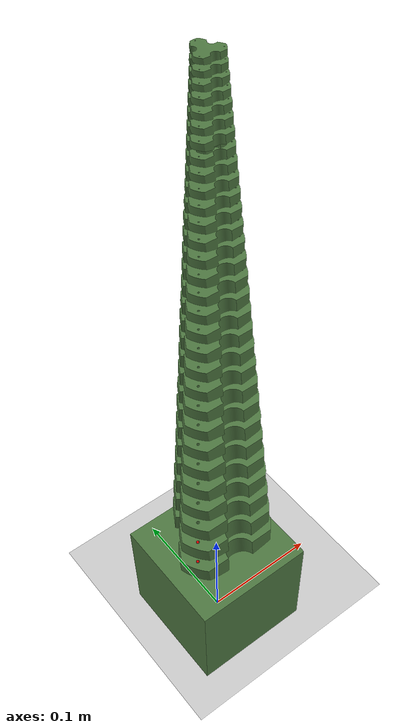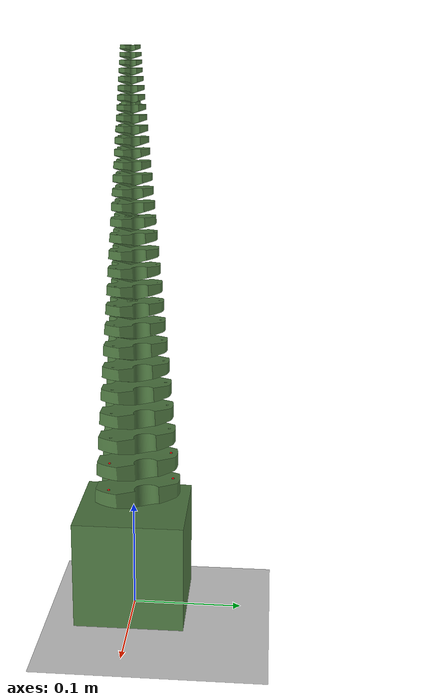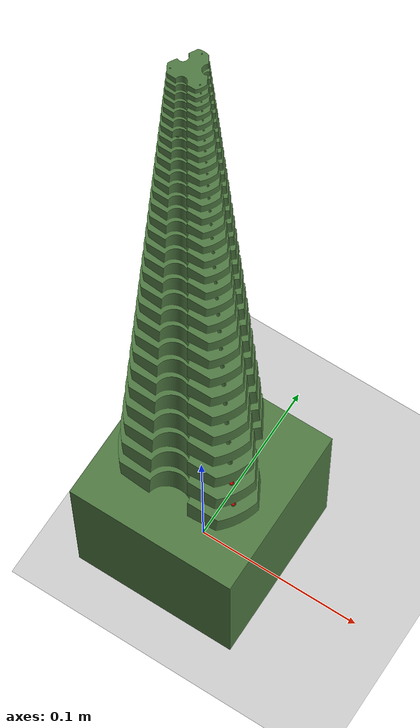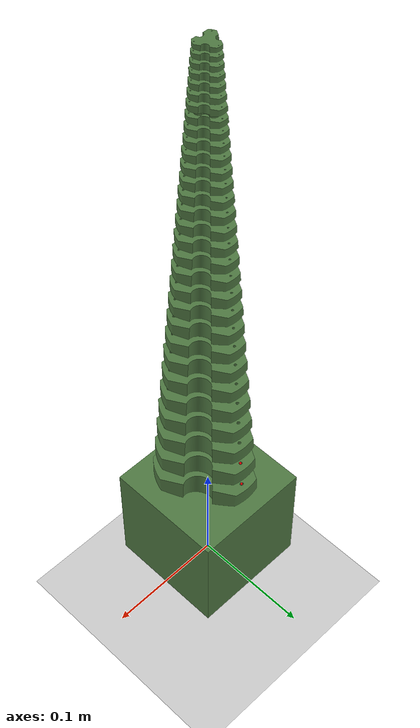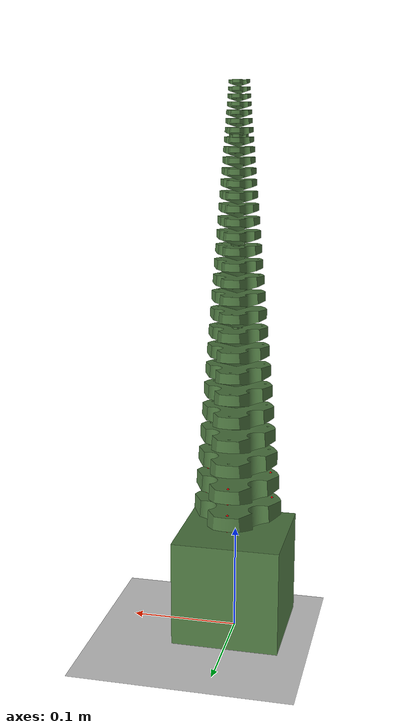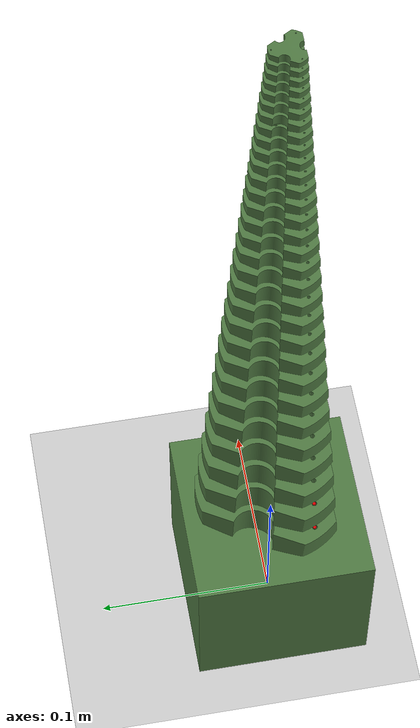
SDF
<?xml version="1.0" ?>
<sdf version="1.9">
  <world name="spirob">
    <physics name="1ms" type="dart">
      <max_step_size>0.001</max_step_size>
      <real_time_factor>1.0</real_time_factor>
      <real_time_update_rate>1000</real_time_update_rate>
      <max_contacts>20</max_contacts>
      <dart>
        <solver>
          <type>dantzig</type>
        </solver>
        <collision_detector>ode</collision_detector>
      </dart>
    </physics>

    <plugin name="gz::sim::systems::Physics"
      filename="gz-sim-physics-system">
    </plugin>
    <plugin name="gz::sim::systems::Sensors"
      filename="gz-sim-sensors-system">
      <render_engine>ogre2</render_engine>
    </plugin>
    <plugin name="gz::sim::systems::UserCommands"
      filename="gz-sim-user-commands-system">
    </plugin>
    <plugin name="gz::sim::systems::SceneBroadcaster"
      filename="gz-sim-scene-broadcaster-system">
    </plugin>
    <plugin name="gz::sim::systems::Imu"
      filename="gz-sim-imu-system">
    </plugin>

    <scene>
      <ambient>1.0 1.0 1.0</ambient>
      <background>0.8 0.8 0.8</background>
      <sky></sky>
    </scene>

    <light type="directional" name="sun">
      <cast_shadows>true</cast_shadows>
      <pose>0 0 10 0 0 0</pose>
      <diffuse>0.8 0.8 0.8 1</diffuse>
      <specular>0.8 0.8 0.8 1</specular>
      <attenuation>
        <range>1000</range>
        <constant>0.9</constant>
        <linear>0.01</linear>
        <quadratic>0.001</quadratic>
      </attenuation>
      <direction>-0.5 0.1 -0.9</direction>
    </light>

    <model name="ground_plane">
      <static>true</static>
      <link name="link">
        <collision name="collision">
          <geometry>
            <plane>
              <normal>0 0 1</normal>
              <size>100 100</size>
            </plane>
          </geometry>
        </collision>
        <visual name="visual">
          <geometry>
            <plane>
              <normal>0 0 1</normal>
              <size>100 100</size>
            </plane>
          </geometry>
          <material>
            <ambient>0.8 0.8 0.8</ambient>
            <diffuse>0.8 0.8 0.8</diffuse>
            <specular>0.1 0.1 0.1</specular>
          </material>
        </visual>
      </link>
    </model>

    <model name="arm">
      <static>0</static>
      <self_collide>1</self_collide>
      <include merge="true">
        <uri>model://spirob_3d</uri>
        <pose degrees="true">0 0 0.05 0 0 0</pose>
      </include>
      <joint name="arm_world" type="fixed">
        <parent>world</parent>
        <child>base_link</child>
      </joint>
    </model>

  </world>
</sdf>

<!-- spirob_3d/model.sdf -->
<sdf version="1.9">
  <model name="spirob_3d">
    <static>0</static>
    <self_collide>1</self_collide>
    <link name="base_link">
      <pose degrees="true">0 0 0 0 0 0</pose>
      <inertial auto="true" />
      <collision name="collision">
        <pose degrees="true">0 0 0 0 0 0</pose>
        <density>10000</density>
        <geometry>
          <box>
            <size>0.1 0.1 0.1</size>
          </box>
        </geometry>
        <surface>
          <friction>
            <ode>
              <mu>1.0</mu>
              <mu2>1.0</mu2>
            </ode>
          </friction>
        </surface>
      </collision>
      <visual name="visual">
        <pose degrees="true">0 0 0 0 0 0</pose>
        <geometry>
          <box>
            <size>0.1 0.1 0.1</size>
          </box>
        </geometry>
        <material>
          <ambient>0.30859375 0.47265625 0.2578125</ambient>
          <diffuse>0.30859375 0.47265625 0.2578125</diffuse>
          <specular>0.1 0.1 0.1</specular>
        </material>
      </visual>
    </link>
    <joint name="joint01" type="fixed">
      <pose degrees="true" relative_to="base_link">0 0 0.05 0 0 0</pose>
      <parent>base_link</parent>
      <child>link1</child>
    </joint>

    <link name="link1">
      <pose degrees="true" relative_to="joint01">0 0 0 0 0 0</pose>
      <inertial auto="true" />
      <collision name="collision">
        <pose degrees="true">0 0 0 0 0 0</pose>
        <density>1100</density>
        <geometry>
          <mesh>
            <scale>0.001000000 0.001000000 0.001000000</scale>
            <uri>meshes/baselink.stl</uri>
          </mesh>
        </geometry>
        <surface>
          <friction>
            <ode>
              <mu>1.0</mu>
              <mu2>1.0</mu2>
            </ode>
          </friction>
        </surface>
      </collision>
      <visual name="visual">
        <pose degrees="true">0 0 0 0 0 0</pose>
        <geometry>
          <mesh>
            <scale>0.001000000 0.001000000 0.001000000</scale>
            <uri>meshes/baselink.stl</uri>
          </mesh>
        </geometry>
        <material>
          <ambient>0.30859375 0.47265625 0.2578125</ambient>
          <diffuse>0.30859375 0.47265625 0.2578125</diffuse>
          <specular>0.1 0.1 0.1</specular>
        </material>
      </visual>
      <visual name="s1_1">
        <pose>0.000000000 0.037646857 0.012545197 0 0 0</pose>
        <geometry>
          <sphere>
            <radius>0.001000</radius>
          </sphere>
        </geometry>
        <material>
          <ambient>1 0 0</ambient>
          <diffuse>1 0 0</diffuse>
          <specular>0.1 0.1 0.1</specular>
        </material>
      </visual>
      <visual name="s1_2">
        <pose>0.000000000 0.036492190 0.027187138 0 0 0</pose>
        <geometry>
          <sphere>
            <radius>0.001000</radius>
          </sphere>
        </geometry>
        <material>
          <ambient>1 0 0</ambient>
          <diffuse>1 0 0</diffuse>
          <specular>0.1 0.1 0.1</specular>
        </material>
      </visual>
      <visual name="s1_3">
        <pose>-0.032603134 -0.018823428 0.012545197 0 0 0</pose>
        <geometry>
          <sphere>
            <radius>0.001000</radius>
          </sphere>
        </geometry>
        <material>
          <ambient>1 0 0</ambient>
          <diffuse>1 0 0</diffuse>
          <specular>0.1 0.1 0.1</specular>
        </material>
      </visual>
      <visual name="s1_4">
        <pose>-0.031603163 -0.018246095 0.027187138 0 0 0</pose>
        <geometry>
          <sphere>
            <radius>0.001000</radius>
          </sphere>
        </geometry>
        <material>
          <ambient>1 0 0</ambient>
          <diffuse>1 0 0</diffuse>
          <specular>0.1 0.1 0.1</specular>
        </material>
      </visual>
      <visual name="s1_5">
        <pose>0.032603134 -0.018823428 0.012545197 0 0 0</pose>
        <geometry>
          <sphere>
            <radius>0.001000</radius>
          </sphere>
        </geometry>
        <material>
          <ambient>1 0 0</ambient>
          <diffuse>1 0 0</diffuse>
          <specular>0.1 0.1 0.1</specular>
        </material>
      </visual>
      <visual name="s1_6">
        <pose>0.031603163 -0.018246095 0.027187138 0 0 0</pose>
        <geometry>
          <sphere>
            <radius>0.001000</radius>
          </sphere>
        </geometry>
        <material>
          <ambient>1 0 0</ambient>
          <diffuse>1 0 0</diffuse>
          <specular>0.1 0.1 0.1</specular>
        </material>
      </visual>
    </link>
    <link name="link2">
      <pose degrees="true" relative_to="joint12">0 0 0 0 0 0</pose>
      <inertial auto="true" />
      <collision name="collision">
        <density>1100</density>
        <pose degrees="true">0 0 0 0 0 0</pose>
        <geometry>
          <mesh>
            <scale>0.000949007 0.000949007 0.000949007</scale>
            <uri>meshes/baselink.stl</uri>
          </mesh>
        </geometry>
        <surface>
          <friction>
            <ode>
              <mu>1.0</mu>
              <mu2>1.0</mu2>
            </ode>
          </friction>
        </surface>
      </collision>
      <visual name="visual">
        <pose degrees="true">0 0 0 0 0 0</pose>
        <geometry>
          <mesh>
            <scale>0.000949007 0.000949007 0.000949007</scale>
            <uri>meshes/baselink.stl</uri>
          </mesh>
        </geometry>
        <material>
          <ambient>0.30859375 0.47265625 0.2578125</ambient>
          <diffuse>0.30859375 0.47265625 0.2578125</diffuse>
          <specular>0.1 0.1 0.1</specular>
        </material>
      </visual>
      <visual name="s2_1">
        <pose>0.000000000 0.035727136 0.011905482 0 0 0</pose>
        <geometry>
          <sphere>
            <radius>0.001000</radius>
          </sphere>
        </geometry>
        <material>
          <ambient>1 0 0</ambient>
          <diffuse>1 0 0</diffuse>
          <specular>0.1 0.1 0.1</specular>
        </material>
      </visual>
      <visual name="s2_2">
        <pose>0.000000000 0.034631350 0.025800788 0 0 0</pose>
        <geometry>
          <sphere>
            <radius>0.001000</radius>
          </sphere>
        </geometry>
        <material>
          <ambient>1 0 0</ambient>
          <diffuse>1 0 0</diffuse>
          <specular>0.1 0.1 0.1</specular>
        </material>
      </visual>
      <visual name="s2_3">
        <pose>-0.030940608 -0.017863568 0.011905482 0 0 0</pose>
        <geometry>
          <sphere>
            <radius>0.001000</radius>
          </sphere>
        </geometry>
        <material>
          <ambient>1 0 0</ambient>
          <diffuse>1 0 0</diffuse>
          <specular>0.1 0.1 0.1</specular>
        </material>
      </visual>
      <visual name="s2_4">
        <pose>-0.029991628 -0.017315675 0.025800788 0 0 0</pose>
        <geometry>
          <sphere>
            <radius>0.001000</radius>
          </sphere>
        </geometry>
        <material>
          <ambient>1 0 0</ambient>
          <diffuse>1 0 0</diffuse>
          <specular>0.1 0.1 0.1</specular>
        </material>
      </visual>
      <visual name="s2_5">
        <pose>0.030940608 -0.017863568 0.011905482 0 0 0</pose>
        <geometry>
          <sphere>
            <radius>0.001000</radius>
          </sphere>
        </geometry>
        <material>
          <ambient>1 0 0</ambient>
          <diffuse>1 0 0</diffuse>
          <specular>0.1 0.1 0.1</specular>
        </material>
      </visual>
      <visual name="s2_6">
        <pose>0.029991628 -0.017315675 0.025800788 0 0 0</pose>
        <geometry>
          <sphere>
            <radius>0.001000</radius>
          </sphere>
        </geometry>
        <material>
          <ambient>1 0 0</ambient>
          <diffuse>1 0 0</diffuse>
          <specular>0.1 0.1 0.1</specular>
        </material>
      </visual>
    </link>
    <link name="link3">
      <pose degrees="true" relative_to="joint23">0 0 0 0 0 0</pose>
      <inertial auto="true" />
      <collision name="collision">
        <pose degrees="true">0 0 0 0 0 0</pose>
        <density>1100</density>
        <geometry>
          <mesh>
            <scale>0.000900615 0.000900615 0.000900615</scale>
            <uri>meshes/baselink.stl</uri>
          </mesh>
        </geometry>
        <surface>
          <friction>
            <ode>
              <mu>1.0</mu>
              <mu2>1.0</mu2>
            </ode>
          </friction>
        </surface>
      </collision>
      <visual name="visual">
        <pose degrees="true">0 0 0 0 0 0</pose>
        <geometry>
          <mesh>
            <scale>0.000900615 0.000900615 0.000900615</scale>
            <uri>meshes/baselink.stl</uri>
          </mesh>
        </geometry>
        <material>
          <ambient>0.30859375 0.47265625 0.2578125</ambient>
          <diffuse>0.30859375 0.47265625 0.2578125</diffuse>
          <specular>0.1 0.1 0.1</specular>
        </material>
      </visual>
    </link>
    <link name="link4">
      <pose degrees="true" relative_to="joint34">0 0 0 0 0 0</pose>
      <inertial auto="true" />
      <collision name="collision">
        <pose degrees="true">0 0 0 0 0 0</pose>
        <density>1100</density>
        <geometry>
          <mesh>
            <scale>0.000854690 0.000854690 0.000854690</scale>
            <uri>meshes/baselink.stl</uri>
          </mesh>
        </geometry>
        <surface>
          <friction>
            <ode>
              <mu>1.0</mu>
              <mu2>1.0</mu2>
            </ode>
          </friction>
        </surface>
      </collision>
      <visual name="visual">
        <pose degrees="true">0 0 0 0 0 0</pose>
        <geometry>
          <mesh>
            <scale>0.000854690 0.000854690 0.000854690</scale>
            <uri>meshes/baselink.stl</uri>
          </mesh>
        </geometry>
        <material>
          <ambient>0.30859375 0.47265625 0.2578125</ambient>
          <diffuse>0.30859375 0.47265625 0.2578125</diffuse>
          <specular>0.1 0.1 0.1</specular>
        </material>
      </visual>
    </link>
    <link name="link5">
      <pose degrees="true" relative_to="joint45">0 0 0 0 0 0</pose>
      <inertial auto="true" />
      <collision name="collision">
        <pose degrees="true">0 0 0 0 0 0</pose>
        <density>1100</density>
        <geometry>
          <mesh>
            <scale>0.000811107 0.000811107 0.000811107</scale>
            <uri>meshes/baselink.stl</uri>
          </mesh>
        </geometry>
        <surface>
          <friction>
            <ode>
              <mu>1.0</mu>
              <mu2>1.0</mu2>
            </ode>
          </friction>
        </surface>
      </collision>
      <visual name="visual">
        <pose degrees="true">0 0 0 0 0 0</pose>
        <geometry>
          <mesh>
            <scale>0.000811107 0.000811107 0.000811107</scale>
            <uri>meshes/baselink.stl</uri>
          </mesh>
        </geometry>
        <material>
          <ambient>0.30859375 0.47265625 0.2578125</ambient>
          <diffuse>0.30859375 0.47265625 0.2578125</diffuse>
          <specular>0.1 0.1 0.1</specular>
        </material>
      </visual>
    </link>
    <link name="link6">
      <pose degrees="true" relative_to="joint56">0 0 0 0 0 0</pose>
      <inertial auto="true" />
      <collision name="collision">
        <pose degrees="true">0 0 0 0 0 0</pose>
        <density>1100</density>
        <geometry>
          <mesh>
            <scale>0.000769746 0.000769746 0.000769746</scale>
            <uri>meshes/baselink.stl</uri>
          </mesh>
        </geometry>
        <surface>
          <friction>
            <ode>
              <mu>1.0</mu>
              <mu2>1.0</mu2>
            </ode>
          </friction>
        </surface>
      </collision>
      <visual name="visual">
        <pose degrees="true">0 0 0 0 0 0</pose>
        <geometry>
          <mesh>
            <scale>0.000769746 0.000769746 0.000769746</scale>
            <uri>meshes/baselink.stl</uri>
          </mesh>
        </geometry>
        <material>
          <ambient>0.30859375 0.47265625 0.2578125</ambient>
          <diffuse>0.30859375 0.47265625 0.2578125</diffuse>
          <specular>0.1 0.1 0.1</specular>
        </material>
      </visual>
    </link>
    <link name="link7">
      <pose degrees="true" relative_to="joint67">0 0 0 0 0 0</pose>
      <inertial auto="true" />
      <collision name="collision">
        <pose degrees="true">0 0 0 0 0 0</pose>
        <density>1100</density>
        <geometry>
          <mesh>
            <scale>0.000730494 0.000730494 0.000730494</scale>
            <uri>meshes/baselink.stl</uri>
          </mesh>
        </geometry>
        <surface>
          <friction>
            <ode>
              <mu>1.0</mu>
              <mu2>1.0</mu2>
            </ode>
          </friction>
        </surface>
      </collision>
      <visual name="visual">
        <pose degrees="true">0 0 0 0 0 0</pose>
        <geometry>
          <mesh>
            <scale>0.000730494 0.000730494 0.000730494</scale>
            <uri>meshes/baselink.stl</uri>
          </mesh>
        </geometry>
        <material>
          <ambient>0.30859375 0.47265625 0.2578125</ambient>
          <diffuse>0.30859375 0.47265625 0.2578125</diffuse>
          <specular>0.1 0.1 0.1</specular>
        </material>
      </visual>
    </link>
    <link name="link8">
      <pose degrees="true" relative_to="joint78">0 0 0 0 0 0</pose>
      <inertial auto="true" />
      <collision name="collision">
        <pose degrees="true">0 0 0 0 0 0</pose>
        <density>1100</density>
        <geometry>
          <mesh>
            <scale>0.000693244 0.000693244 0.000693244</scale>
            <uri>meshes/baselink.stl</uri>
          </mesh>
        </geometry>
        <surface>
          <friction>
            <ode>
              <mu>1.0</mu>
              <mu2>1.0</mu2>
            </ode>
          </friction>
        </surface>
      </collision>
      <visual name="visual">
        <pose degrees="true">0 0 0 0 0 0</pose>
        <geometry>
          <mesh>
            <scale>0.000693244 0.000693244 0.000693244</scale>
            <uri>meshes/baselink.stl</uri>
          </mesh>
        </geometry>
        <material>
          <ambient>0.30859375 0.47265625 0.2578125</ambient>
          <diffuse>0.30859375 0.47265625 0.2578125</diffuse>
          <specular>0.1 0.1 0.1</specular>
        </material>
      </visual>
    </link>
    <link name="link9">
      <pose degrees="true" relative_to="joint89">0 0 0 0 0 0</pose>
      <inertial auto="true" />
      <collision name="collision">
        <pose degrees="true">0 0 0 0 0 0</pose>
        <density>1100</density>
        <geometry>
          <mesh>
            <scale>0.000657894 0.000657894 0.000657894</scale>
            <uri>meshes/baselink.stl</uri>
          </mesh>
        </geometry>
        <surface>
          <friction>
            <ode>
              <mu>1.0</mu>
              <mu2>1.0</mu2>
            </ode>
          </friction>
        </surface>
      </collision>
      <visual name="visual">
        <pose degrees="true">0 0 0 0 0 0</pose>
        <geometry>
          <mesh>
            <scale>0.000657894 0.000657894 0.000657894</scale>
            <uri>meshes/baselink.stl</uri>
          </mesh>
        </geometry>
        <material>
          <ambient>0.30859375 0.47265625 0.2578125</ambient>
          <diffuse>0.30859375 0.47265625 0.2578125</diffuse>
          <specular>0.1 0.1 0.1</specular>
        </material>
      </visual>
    </link>
    <link name="link10">
      <pose degrees="true" relative_to="joint910">0 0 0 0 0 0</pose>
      <inertial auto="true" />
      <collision name="collision">
        <pose degrees="true">0 0 0 0 0 0</pose>
        <density>1100</density>
        <geometry>
          <mesh>
            <scale>0.000624346 0.000624346 0.000624346</scale>
            <uri>meshes/baselink.stl</uri>
          </mesh>
        </geometry>
        <surface>
          <friction>
            <ode>
              <mu>1.0</mu>
              <mu2>1.0</mu2>
            </ode>
          </friction>
        </surface>
      </collision>
      <visual name="visual">
        <pose degrees="true">0 0 0 0 0 0</pose>
        <geometry>
          <mesh>
            <scale>0.000624346 0.000624346 0.000624346</scale>
            <uri>meshes/baselink.stl</uri>
          </mesh>
        </geometry>
        <material>
          <ambient>0.30859375 0.47265625 0.2578125</ambient>
          <diffuse>0.30859375 0.47265625 0.2578125</diffuse>
          <specular>0.1 0.1 0.1</specular>
        </material>
      </visual>
    </link>
    <link name="link11">
      <pose degrees="true" relative_to="joint1011">0 0 0 0 0 0</pose>
      <inertial auto="true" />
      <collision name="collision">
        <pose degrees="true">0 0 0 0 0 0</pose>
        <density>1100</density>
        <geometry>
          <mesh>
            <scale>0.000592509 0.000592509 0.000592509</scale>
            <uri>meshes/baselink.stl</uri>
          </mesh>
        </geometry>
        <surface>
          <friction>
            <ode>
              <mu>1.0</mu>
              <mu2>1.0</mu2>
            </ode>
          </friction>
        </surface>
      </collision>
      <visual name="visual">
        <pose degrees="true">0 0 0 0 0 0</pose>
        <geometry>
          <mesh>
            <scale>0.000592509 0.000592509 0.000592509</scale>
            <uri>meshes/baselink.stl</uri>
          </mesh>
        </geometry>
        <material>
          <ambient>0.30859375 0.47265625 0.2578125</ambient>
          <diffuse>0.30859375 0.47265625 0.2578125</diffuse>
          <specular>0.1 0.1 0.1</specular>
        </material>
      </visual>
    </link>
    <link name="link12">
      <pose degrees="true" relative_to="joint1112">0 0 0 0 0 0</pose>
      <inertial auto="true" />
      <collision name="collision">
        <pose degrees="true">0 0 0 0 0 0</pose>
        <density>1100</density>
        <geometry>
          <mesh>
            <scale>0.000562295 0.000562295 0.000562295</scale>
            <uri>meshes/baselink.stl</uri>
          </mesh>
        </geometry>
        <surface>
          <friction>
            <ode>
              <mu>1.0</mu>
              <mu2>1.0</mu2>
            </ode>
          </friction>
        </surface>
      </collision>
      <visual name="visual">
        <pose degrees="true">0 0 0 0 0 0</pose>
        <geometry>
          <mesh>
            <scale>0.000562295 0.000562295 0.000562295</scale>
            <uri>meshes/baselink.stl</uri>
          </mesh>
        </geometry>
        <material>
          <ambient>0.30859375 0.47265625 0.2578125</ambient>
          <diffuse>0.30859375 0.47265625 0.2578125</diffuse>
          <specular>0.1 0.1 0.1</specular>
        </material>
      </visual>
    </link>
    <link name="link13">
      <pose degrees="true" relative_to="joint1213">0 0 0 0 0 0</pose>
      <inertial auto="true" />
      <collision name="collision">
        <pose degrees="true">0 0 0 0 0 0</pose>
        <density>1100</density>
        <geometry>
          <mesh>
            <scale>0.000533622 0.000533622 0.000533622</scale>
            <uri>meshes/baselink.stl</uri>
          </mesh>
        </geometry>
        <surface>
          <friction>
            <ode>
              <mu>1.0</mu>
              <mu2>1.0</mu2>
            </ode>
          </friction>
        </surface>
      </collision>
      <visual name="visual">
        <pose degrees="true">0 0 0 0 0 0</pose>
        <geometry>
          <mesh>
            <scale>0.000533622 0.000533622 0.000533622</scale>
            <uri>meshes/baselink.stl</uri>
          </mesh>
        </geometry>
        <material>
          <ambient>0.30859375 0.47265625 0.2578125</ambient>
          <diffuse>0.30859375 0.47265625 0.2578125</diffuse>
          <specular>0.1 0.1 0.1</specular>
        </material>
      </visual>
    </link>
    <link name="link14">
      <pose degrees="true" relative_to="joint1314">0 0 0 0 0 0</pose>
      <inertial auto="true" />
      <collision name="collision">
        <pose degrees="true">0 0 0 0 0 0</pose>
        <density>1100</density>
        <geometry>
          <mesh>
            <scale>0.000506411 0.000506411 0.000506411</scale>
            <uri>meshes/baselink.stl</uri>
          </mesh>
        </geometry>
        <surface>
          <friction>
            <ode>
              <mu>1.0</mu>
              <mu2>1.0</mu2>
            </ode>
          </friction>
        </surface>
      </collision>
      <visual name="visual">
        <pose degrees="true">0 0 0 0 0 0</pose>
        <geometry>
          <mesh>
            <scale>0.000506411 0.000506411 0.000506411</scale>
            <uri>meshes/baselink.stl</uri>
          </mesh>
        </geometry>
        <material>
          <ambient>0.30859375 0.47265625 0.2578125</ambient>
          <diffuse>0.30859375 0.47265625 0.2578125</diffuse>
          <specular>0.1 0.1 0.1</specular>
        </material>
      </visual>
    </link>
    <link name="link15">
      <pose degrees="true" relative_to="joint1415">0 0 0 0 0 0</pose>
      <inertial auto="true" />
      <collision name="collision">
        <pose degrees="true">0 0 0 0 0 0</pose>
        <density>1100</density>
        <geometry>
          <mesh>
            <scale>0.000480588 0.000480588 0.000480588</scale>
            <uri>meshes/baselink.stl</uri>
          </mesh>
        </geometry>
        <surface>
          <friction>
            <ode>
              <mu>1.0</mu>
              <mu2>1.0</mu2>
            </ode>
          </friction>
        </surface>
      </collision>
      <visual name="visual">
        <pose degrees="true">0 0 0 0 0 0</pose>
        <geometry>
          <mesh>
            <scale>0.000480588 0.000480588 0.000480588</scale>
            <uri>meshes/baselink.stl</uri>
          </mesh>
        </geometry>
        <material>
          <ambient>0.30859375 0.47265625 0.2578125</ambient>
          <diffuse>0.30859375 0.47265625 0.2578125</diffuse>
          <specular>0.1 0.1 0.1</specular>
        </material>
      </visual>
    </link>
    <link name="link16">
      <pose degrees="true" relative_to="joint1516">0 0 0 0 0 0</pose>
      <inertial auto="true" />
      <collision name="collision">
        <pose degrees="true">0 0 0 0 0 0</pose>
        <density>1100</density>
        <geometry>
          <mesh>
            <scale>0.000456081 0.000456081 0.000456081</scale>
            <uri>meshes/baselink.stl</uri>
          </mesh>
        </geometry>
        <surface>
          <friction>
            <ode>
              <mu>1.0</mu>
              <mu2>1.0</mu2>
            </ode>
          </friction>
        </surface>
      </collision>
      <visual name="visual">
        <pose degrees="true">0 0 0 0 0 0</pose>
        <geometry>
          <mesh>
            <scale>0.000456081 0.000456081 0.000456081</scale>
            <uri>meshes/baselink.stl</uri>
          </mesh>
        </geometry>
        <material>
          <ambient>0.30859375 0.47265625 0.2578125</ambient>
          <diffuse>0.30859375 0.47265625 0.2578125</diffuse>
          <specular>0.1 0.1 0.1</specular>
        </material>
      </visual>
    </link>
    <link name="link17">
      <pose degrees="true" relative_to="joint1617">0 0 0 0 0 0</pose>
      <inertial auto="true" />
      <collision name="collision">
        <pose degrees="true">0 0 0 0 0 0</pose>
        <density>1100</density>
        <geometry>
          <mesh>
            <scale>0.000432825 0.000432825 0.000432825</scale>
            <uri>meshes/baselink.stl</uri>
          </mesh>
        </geometry>
        <surface>
          <friction>
            <ode>
              <mu>1.0</mu>
              <mu2>1.0</mu2>
            </ode>
          </friction>
        </surface>
      </collision>
      <visual name="visual">
        <pose degrees="true">0 0 0 0 0 0</pose>
        <geometry>
          <mesh>
            <scale>0.000432825 0.000432825 0.000432825</scale>
            <uri>meshes/baselink.stl</uri>
          </mesh>
        </geometry>
        <material>
          <ambient>0.30859375 0.47265625 0.2578125</ambient>
          <diffuse>0.30859375 0.47265625 0.2578125</diffuse>
          <specular>0.1 0.1 0.1</specular>
        </material>
      </visual>
    </link>
    <link name="link18">
      <pose degrees="true" relative_to="joint1718">0 0 0 0 0 0</pose>
      <inertial auto="true" />
      <collision name="collision">
        <pose degrees="true">0 0 0 0 0 0</pose>
        <density>1100</density>
        <geometry>
          <mesh>
            <scale>0.000410754 0.000410754 0.000410754</scale>
            <uri>meshes/baselink.stl</uri>
          </mesh>
        </geometry>
        <surface>
          <friction>
            <ode>
              <mu>1.0</mu>
              <mu2>1.0</mu2>
            </ode>
          </friction>
        </surface>
      </collision>
      <visual name="visual">
        <pose degrees="true">0 0 0 0 0 0</pose>
        <geometry>
          <mesh>
            <scale>0.000410754 0.000410754 0.000410754</scale>
            <uri>meshes/baselink.stl</uri>
          </mesh>
        </geometry>
        <material>
          <ambient>0.30859375 0.47265625 0.2578125</ambient>
          <diffuse>0.30859375 0.47265625 0.2578125</diffuse>
          <specular>0.1 0.1 0.1</specular>
        </material>
      </visual>
    </link>
    <link name="link19">
      <pose degrees="true" relative_to="joint1819">0 0 0 0 0 0</pose>
      <inertial auto="true" />
      <collision name="collision">
        <pose degrees="true">0 0 0 0 0 0</pose>
        <density>1100</density>
        <geometry>
          <mesh>
            <scale>0.000389808 0.000389808 0.000389808</scale>
            <uri>meshes/baselink.stl</uri>
          </mesh>
        </geometry>
        <surface>
          <friction>
            <ode>
              <mu>1.0</mu>
              <mu2>1.0</mu2>
            </ode>
          </friction>
        </surface>
      </collision>
      <visual name="visual">
        <pose degrees="true">0 0 0 0 0 0</pose>
        <geometry>
          <mesh>
            <scale>0.000389808 0.000389808 0.000389808</scale>
            <uri>meshes/baselink.stl</uri>
          </mesh>
        </geometry>
        <material>
          <ambient>0.30859375 0.47265625 0.2578125</ambient>
          <diffuse>0.30859375 0.47265625 0.2578125</diffuse>
          <specular>0.1 0.1 0.1</specular>
        </material>
      </visual>
    </link>
    <link name="link20">
      <pose degrees="true" relative_to="joint1920">0 0 0 0 0 0</pose>
      <inertial auto="true" />
      <collision name="collision">
        <pose degrees="true">0 0 0 0 0 0</pose>
        <density>1100</density>
        <geometry>
          <mesh>
            <scale>0.000369931 0.000369931 0.000369931</scale>
            <uri>meshes/baselink.stl</uri>
          </mesh>
        </geometry>
        <surface>
          <friction>
            <ode>
              <mu>1.0</mu>
              <mu2>1.0</mu2>
            </ode>
          </friction>
        </surface>
      </collision>
      <visual name="visual">
        <pose degrees="true">0 0 0 0 0 0</pose>
        <geometry>
          <mesh>
            <scale>0.000369931 0.000369931 0.000369931</scale>
            <uri>meshes/baselink.stl</uri>
          </mesh>
        </geometry>
        <material>
          <ambient>0.30859375 0.47265625 0.2578125</ambient>
          <diffuse>0.30859375 0.47265625 0.2578125</diffuse>
          <specular>0.1 0.1 0.1</specular>
        </material>
      </visual>
    </link>
    <link name="link21">
      <pose degrees="true" relative_to="joint2021">0 0 0 0 0 0</pose>
      <inertial auto="true" />
      <collision name="collision">
        <pose degrees="true">0 0 0 0 0 0</pose>
        <density>1100</density>
        <geometry>
          <mesh>
            <scale>0.000351067 0.000351067 0.000351067</scale>
            <uri>meshes/baselink.stl</uri>
          </mesh>
        </geometry>
        <surface>
          <friction>
            <ode>
              <mu>1.0</mu>
              <mu2>1.0</mu2>
            </ode>
          </friction>
        </surface>
      </collision>
      <visual name="visual">
        <pose degrees="true">0 0 0 0 0 0</pose>
        <geometry>
          <mesh>
            <scale>0.000351067 0.000351067 0.000351067</scale>
            <uri>meshes/baselink.stl</uri>
          </mesh>
        </geometry>
        <material>
          <ambient>0.30859375 0.47265625 0.2578125</ambient>
          <diffuse>0.30859375 0.47265625 0.2578125</diffuse>
          <specular>0.1 0.1 0.1</specular>
        </material>
      </visual>
    </link>
    <link name="link22">
      <pose degrees="true" relative_to="joint2122">0 0 0 0 0 0</pose>
      <inertial auto="true" />
      <collision name="collision">
        <pose degrees="true">0 0 0 0 0 0</pose>
        <density>1100</density>
        <geometry>
          <mesh>
            <scale>0.000333165 0.000333165 0.000333165</scale>
            <uri>meshes/baselink.stl</uri>
          </mesh>
        </geometry>
        <surface>
          <friction>
            <ode>
              <mu>1.0</mu>
              <mu2>1.0</mu2>
            </ode>
          </friction>
        </surface>
      </collision>
      <visual name="visual">
        <pose degrees="true">0 0 0 0 0 0</pose>
        <geometry>
          <mesh>
            <scale>0.000333165 0.000333165 0.000333165</scale>
            <uri>meshes/baselink.stl</uri>
          </mesh>
        </geometry>
        <material>
          <ambient>0.30859375 0.47265625 0.2578125</ambient>
          <diffuse>0.30859375 0.47265625 0.2578125</diffuse>
          <specular>0.1 0.1 0.1</specular>
        </material>
      </visual>
    </link>
    <link name="link23">
      <pose degrees="true" relative_to="joint2223">0 0 0 0 0 0</pose>
      <inertial auto="true" />
      <collision name="collision">
        <pose degrees="true">0 0 0 0 0 0</pose>
        <density>1100</density>
        <geometry>
          <mesh>
            <scale>0.000316176 0.000316176 0.000316176</scale>
            <uri>meshes/baselink.stl</uri>
          </mesh>
        </geometry>
        <surface>
          <friction>
            <ode>
              <mu>1.0</mu>
              <mu2>1.0</mu2>
            </ode>
          </friction>
        </surface>
      </collision>
      <visual name="visual">
        <pose degrees="true">0 0 0 0 0 0</pose>
        <geometry>
          <mesh>
            <scale>0.000316176 0.000316176 0.000316176</scale>
            <uri>meshes/baselink.stl</uri>
          </mesh>
        </geometry>
        <material>
          <ambient>0.30859375 0.47265625 0.2578125</ambient>
          <diffuse>0.30859375 0.47265625 0.2578125</diffuse>
          <specular>0.1 0.1 0.1</specular>
        </material>
      </visual>
    </link>
    <link name="link24">
      <pose degrees="true" relative_to="joint2324">0 0 0 0 0 0</pose>
      <inertial auto="true" />
      <collision name="collision">
        <pose degrees="true">0 0 0 0 0 0</pose>
        <density>1100</density>
        <geometry>
          <mesh>
            <scale>0.000300053 0.000300053 0.000300053</scale>
            <uri>meshes/baselink.stl</uri>
          </mesh>
        </geometry>
        <surface>
          <friction>
            <ode>
              <mu>1.0</mu>
              <mu2>1.0</mu2>
            </ode>
          </friction>
        </surface>
      </collision>
      <visual name="visual">
        <pose degrees="true">0 0 0 0 0 0</pose>
        <geometry>
          <mesh>
            <scale>0.000300053 0.000300053 0.000300053</scale>
            <uri>meshes/baselink.stl</uri>
          </mesh>
        </geometry>
        <material>
          <ambient>0.30859375 0.47265625 0.2578125</ambient>
          <diffuse>0.30859375 0.47265625 0.2578125</diffuse>
          <specular>0.1 0.1 0.1</specular>
        </material>
      </visual>
    </link>
    <link name="link25">
      <pose degrees="true" relative_to="joint2425">0 0 0 0 0 0</pose>
      <inertial auto="true" />
      <collision name="collision">
        <pose degrees="true">0 0 0 0 0 0</pose>
        <density>1100</density>
        <geometry>
          <mesh>
            <scale>0.000284753 0.000284753 0.000284753</scale>
            <uri>meshes/baselink.stl</uri>
          </mesh>
        </geometry>
        <surface>
          <friction>
            <ode>
              <mu>1.0</mu>
              <mu2>1.0</mu2>
            </ode>
          </friction>
        </surface>
      </collision>
      <visual name="visual">
        <pose degrees="true">0 0 0 0 0 0</pose>
        <geometry>
          <mesh>
            <scale>0.000284753 0.000284753 0.000284753</scale>
            <uri>meshes/baselink.stl</uri>
          </mesh>
        </geometry>
        <material>
          <ambient>0.30859375 0.47265625 0.2578125</ambient>
          <diffuse>0.30859375 0.47265625 0.2578125</diffuse>
          <specular>0.1 0.1 0.1</specular>
        </material>
      </visual>
    </link>
    <link name="link26">
      <pose degrees="true" relative_to="joint2526">0 0 0 0 0 0</pose>
      <inertial auto="true" />
      <collision name="collision">
        <pose degrees="true">0 0 0 0 0 0</pose>
        <density>1100</density>
        <geometry>
          <mesh>
            <scale>0.000270232 0.000270232 0.000270232</scale>
            <uri>meshes/baselink.stl</uri>
          </mesh>
        </geometry>
        <surface>
          <friction>
            <ode>
              <mu>1.0</mu>
              <mu2>1.0</mu2>
            </ode>
          </friction>
        </surface>
      </collision>
      <visual name="visual">
        <pose degrees="true">0 0 0 0 0 0</pose>
        <geometry>
          <mesh>
            <scale>0.000270232 0.000270232 0.000270232</scale>
            <uri>meshes/baselink.stl</uri>
          </mesh>
        </geometry>
        <material>
          <ambient>0.30859375 0.47265625 0.2578125</ambient>
          <diffuse>0.30859375 0.47265625 0.2578125</diffuse>
          <specular>0.1 0.1 0.1</specular>
        </material>
      </visual>
    </link>
    <link name="link27">
      <pose degrees="true" relative_to="joint2627">0 0 0 0 0 0</pose>
      <inertial auto="true" />
      <collision name="collision">
        <pose degrees="true">0 0 0 0 0 0</pose>
        <density>1100</density>
        <geometry>
          <mesh>
            <scale>0.000256452 0.000256452 0.000256452</scale>
            <uri>meshes/baselink.stl</uri>
          </mesh>
        </geometry>
        <surface>
          <friction>
            <ode>
              <mu>1.0</mu>
              <mu2>1.0</mu2>
            </ode>
          </friction>
        </surface>
      </collision>
      <visual name="visual">
        <pose degrees="true">0 0 0 0 0 0</pose>
        <geometry>
          <mesh>
            <scale>0.000256452 0.000256452 0.000256452</scale>
            <uri>meshes/baselink.stl</uri>
          </mesh>
        </geometry>
        <material>
          <ambient>0.30859375 0.47265625 0.2578125</ambient>
          <diffuse>0.30859375 0.47265625 0.2578125</diffuse>
          <specular>0.1 0.1 0.1</specular>
        </material>
      </visual>
    </link>
    <link name="link28">
      <pose degrees="true" relative_to="joint2728">0 0 0 0 0 0</pose>
      <inertial auto="true" />
      <collision name="collision">
        <pose degrees="true">0 0 0 0 0 0</pose>
        <density>1100</density>
        <geometry>
          <mesh>
            <scale>0.000243375 0.000243375 0.000243375</scale>
            <uri>meshes/baselink.stl</uri>
          </mesh>
        </geometry>
        <surface>
          <friction>
            <ode>
              <mu>1.0</mu>
              <mu2>1.0</mu2>
            </ode>
          </friction>
        </surface>
      </collision>
      <visual name="visual">
        <pose degrees="true">0 0 0 0 0 0</pose>
        <geometry>
          <mesh>
            <scale>0.000243375 0.000243375 0.000243375</scale>
            <uri>meshes/baselink.stl</uri>
          </mesh>
        </geometry>
        <material>
          <ambient>0.30859375 0.47265625 0.2578125</ambient>
          <diffuse>0.30859375 0.47265625 0.2578125</diffuse>
          <specular>0.1 0.1 0.1</specular>
        </material>
      </visual>
    </link>
    <link name="link29">
      <pose degrees="true" relative_to="joint2829">0 0 0 0 0 0</pose>
      <inertial auto="true" />
      <collision name="collision">
        <pose degrees="true">0 0 0 0 0 0</pose>
        <density>1100</density>
        <geometry>
          <mesh>
            <scale>0.000230965 0.000230965 0.000230965</scale>
            <uri>meshes/baselink.stl</uri>
          </mesh>
        </geometry>
        <surface>
          <friction>
            <ode>
              <mu>1.0</mu>
              <mu2>1.0</mu2>
            </ode>
          </friction>
        </surface>
      </collision>
      <visual name="visual">
        <pose degrees="true">0 0 0 0 0 0</pose>
        <geometry>
          <mesh>
            <scale>0.000230965 0.000230965 0.000230965</scale>
            <uri>meshes/baselink.stl</uri>
          </mesh>
        </geometry>
        <material>
          <ambient>0.30859375 0.47265625 0.2578125</ambient>
          <diffuse>0.30859375 0.47265625 0.2578125</diffuse>
          <specular>0.1 0.1 0.1</specular>
        </material>
      </visual>
    </link>
    <link name="link30">
      <pose degrees="true" relative_to="joint2930">0 0 0 0 0 0</pose>
      <inertial auto="true" />
      <collision name="collision">
        <pose degrees="true">0 0 0 0 0 0</pose>
        <density>1100</density>
        <geometry>
          <mesh>
            <scale>0.000219187 0.000219187 0.000219187</scale>
            <uri>meshes/baselink.stl</uri>
          </mesh>
        </geometry>
        <surface>
          <friction>
            <ode>
              <mu>1.0</mu>
              <mu2>1.0</mu2>
            </ode>
          </friction>
        </surface>
      </collision>
      <visual name="visual">
        <pose degrees="true">0 0 0 0 0 0</pose>
        <geometry>
          <mesh>
            <scale>0.000219187 0.000219187 0.000219187</scale>
            <uri>meshes/baselink.stl</uri>
          </mesh>
        </geometry>
        <material>
          <ambient>0.30859375 0.47265625 0.2578125</ambient>
          <diffuse>0.30859375 0.47265625 0.2578125</diffuse>
          <specular>0.1 0.1 0.1</specular>
        </material>
      </visual>
    </link>
    <link name="link31">
      <pose degrees="true" relative_to="joint3031">0 0 0 0 0 0</pose>
      <inertial auto="true" />
      <collision name="collision">
        <pose degrees="true">0 0 0 0 0 0</pose>
        <density>1100</density>
        <geometry>
          <mesh>
            <scale>0.000208010 0.000208010 0.000208010</scale>
            <uri>meshes/baselink.stl</uri>
          </mesh>
        </geometry>
        <surface>
          <friction>
            <ode>
              <mu>1.0</mu>
              <mu2>1.0</mu2>
            </ode>
          </friction>
        </surface>
      </collision>
      <visual name="visual">
        <pose degrees="true">0 0 0 0 0 0</pose>
        <geometry>
          <mesh>
            <scale>0.000208010 0.000208010 0.000208010</scale>
            <uri>meshes/baselink.stl</uri>
          </mesh>
        </geometry>
        <material>
          <ambient>0.30859375 0.47265625 0.2578125</ambient>
          <diffuse>0.30859375 0.47265625 0.2578125</diffuse>
          <specular>0.1 0.1 0.1</specular>
        </material>
      </visual>
    </link>
    <link name="link32">
      <pose degrees="true" relative_to="joint3132">0 0 0 0 0 0</pose>
      <inertial auto="true" />
      <collision name="collision">
        <pose degrees="true">0 0 0 0 0 0</pose>
        <density>1100</density>
        <geometry>
          <mesh>
            <scale>0.000197403 0.000197403 0.000197403</scale>
            <uri>meshes/baselink.stl</uri>
          </mesh>
        </geometry>
        <surface>
          <friction>
            <ode>
              <mu>1.0</mu>
              <mu2>1.0</mu2>
            </ode>
          </friction>
        </surface>
      </collision>
      <visual name="visual">
        <pose degrees="true">0 0 0 0 0 0</pose>
        <geometry>
          <mesh>
            <scale>0.000197403 0.000197403 0.000197403</scale>
            <uri>meshes/baselink.stl</uri>
          </mesh>
        </geometry>
        <material>
          <ambient>0.30859375 0.47265625 0.2578125</ambient>
          <diffuse>0.30859375 0.47265625 0.2578125</diffuse>
          <specular>0.1 0.1 0.1</specular>
        </material>
      </visual>
    </link>
    <link name="link33">
      <pose degrees="true" relative_to="joint3233">0 0 0 0 0 0</pose>
      <inertial auto="true" />
      <collision name="collision">
        <pose degrees="true">0 0 0 0 0 0</pose>
        <density>1100</density>
        <geometry>
          <mesh>
            <scale>0.000187337 0.000187337 0.000187337</scale>
            <uri>meshes/baselink.stl</uri>
          </mesh>
        </geometry>
        <surface>
          <friction>
            <ode>
              <mu>1.0</mu>
              <mu2>1.0</mu2>
            </ode>
          </friction>
        </surface>
      </collision>
      <visual name="visual">
        <pose degrees="true">0 0 0 0 0 0</pose>
        <geometry>
          <mesh>
            <scale>0.000187337 0.000187337 0.000187337</scale>
            <uri>meshes/baselink.stl</uri>
          </mesh>
        </geometry>
        <material>
          <ambient>0.30859375 0.47265625 0.2578125</ambient>
          <diffuse>0.30859375 0.47265625 0.2578125</diffuse>
          <specular>0.1 0.1 0.1</specular>
        </material>
      </visual>
    </link>
    <link name="link34">
      <pose degrees="true" relative_to="joint3334">0 0 0 0 0 0</pose>
      <inertial auto="true" />
      <collision name="collision">
        <pose degrees="true">0 0 0 0 0 0</pose>
        <density>1100</density>
        <geometry>
          <mesh>
            <scale>0.000177784 0.000177784 0.000177784</scale>
            <uri>meshes/baselink.stl</uri>
          </mesh>
        </geometry>
        <surface>
          <friction>
            <ode>
              <mu>1.0</mu>
              <mu2>1.0</mu2>
            </ode>
          </friction>
        </surface>
      </collision>
      <visual name="visual">
        <pose degrees="true">0 0 0 0 0 0</pose>
        <geometry>
          <mesh>
            <scale>0.000177784 0.000177784 0.000177784</scale>
            <uri>meshes/baselink.stl</uri>
          </mesh>
        </geometry>
        <material>
          <ambient>0.30859375 0.47265625 0.2578125</ambient>
          <diffuse>0.30859375 0.47265625 0.2578125</diffuse>
          <specular>0.1 0.1 0.1</specular>
        </material>
      </visual>
    </link>
    <link name="link35">
      <pose degrees="true" relative_to="joint3435">0 0 0 0 0 0</pose>
      <inertial auto="true" />
      <collision name="collision">
        <pose degrees="true">0 0 0 0 0 0</pose>
        <density>1100</density>
        <geometry>
          <mesh>
            <scale>0.000168718 0.000168718 0.000168718</scale>
            <uri>meshes/baselink.stl</uri>
          </mesh>
        </geometry>
        <surface>
          <friction>
            <ode>
              <mu>1.0</mu>
              <mu2>1.0</mu2>
            </ode>
          </friction>
        </surface>
      </collision>
      <visual name="visual">
        <pose degrees="true">0 0 0 0 0 0</pose>
        <geometry>
          <mesh>
            <scale>0.000168718 0.000168718 0.000168718</scale>
            <uri>meshes/baselink.stl</uri>
          </mesh>
        </geometry>
        <material>
          <ambient>0.30859375 0.47265625 0.2578125</ambient>
          <diffuse>0.30859375 0.47265625 0.2578125</diffuse>
          <specular>0.1 0.1 0.1</specular>
        </material>
      </visual>
    </link>
    <link name="link36">
      <pose degrees="true" relative_to="joint3536">0 0 0 0 0 0</pose>
      <inertial auto="true" />
      <collision name="collision">
        <pose degrees="true">0 0 0 0 0 0</pose>
        <density>1100</density>
        <geometry>
          <mesh>
            <scale>0.000160115 0.000160115 0.000160115</scale>
            <uri>meshes/baselink.stl</uri>
          </mesh>
        </geometry>
        <surface>
          <friction>
            <ode>
              <mu>1.0</mu>
              <mu2>1.0</mu2>
            </ode>
          </friction>
        </surface>
      </collision>
      <visual name="visual">
        <pose degrees="true">0 0 0 0 0 0</pose>
        <geometry>
          <mesh>
            <scale>0.000160115 0.000160115 0.000160115</scale>
            <uri>meshes/baselink.stl</uri>
          </mesh>
        </geometry>
        <material>
          <ambient>0.30859375 0.47265625 0.2578125</ambient>
          <diffuse>0.30859375 0.47265625 0.2578125</diffuse>
          <specular>0.1 0.1 0.1</specular>
        </material>
      </visual>
    </link>
    <link name="link37">
      <pose degrees="true" relative_to="joint3637">0 0 0 0 0 0</pose>
      <inertial auto="true" />
      <collision name="collision">
        <pose degrees="true">0 0 0 0 0 0</pose>
        <density>1100</density>
        <geometry>
          <mesh>
            <scale>0.000151950 0.000151950 0.000151950</scale>
            <uri>meshes/baselink.stl</uri>
          </mesh>
        </geometry>
        <surface>
          <friction>
            <ode>
              <mu>1.0</mu>
              <mu2>1.0</mu2>
            </ode>
          </friction>
        </surface>
      </collision>
      <visual name="visual">
        <pose degrees="true">0 0 0 0 0 0</pose>
        <geometry>
          <mesh>
            <scale>0.000151950 0.000151950 0.000151950</scale>
            <uri>meshes/baselink.stl</uri>
          </mesh>
        </geometry>
        <material>
          <ambient>0.30859375 0.47265625 0.2578125</ambient>
          <diffuse>0.30859375 0.47265625 0.2578125</diffuse>
          <specular>0.1 0.1 0.1</specular>
        </material>
      </visual>
    </link>
    <link name="link38">
      <pose degrees="true" relative_to="joint3738">0 0 0 0 0 0</pose>
      <inertial auto="true" />
      <collision name="collision">
        <pose degrees="true">0 0 0 0 0 0</pose>
        <density>1100</density>
        <geometry>
          <mesh>
            <scale>0.000144202 0.000144202 0.000144202</scale>
            <uri>meshes/baselink.stl</uri>
          </mesh>
        </geometry>
        <surface>
          <friction>
            <ode>
              <mu>1.0</mu>
              <mu2>1.0</mu2>
            </ode>
          </friction>
        </surface>
      </collision>
      <visual name="visual">
        <pose degrees="true">0 0 0 0 0 0</pose>
        <geometry>
          <mesh>
            <scale>0.000144202 0.000144202 0.000144202</scale>
            <uri>meshes/baselink.stl</uri>
          </mesh>
        </geometry>
        <material>
          <ambient>0.30859375 0.47265625 0.2578125</ambient>
          <diffuse>0.30859375 0.47265625 0.2578125</diffuse>
          <specular>0.1 0.1 0.1</specular>
        </material>
      </visual>
    </link>
    <link name="link39">
      <pose degrees="true" relative_to="joint3839">0 0 0 0 0 0</pose>
      <inertial auto="true" />
      <collision name="collision">
        <pose degrees="true">0 0 0 0 0 0</pose>
        <density>1100</density>
        <geometry>
          <mesh>
            <scale>0.000136849 0.000136849 0.000136849</scale>
            <uri>meshes/baselink.stl</uri>
          </mesh>
        </geometry>
        <surface>
          <friction>
            <ode>
              <mu>1.0</mu>
              <mu2>1.0</mu2>
            </ode>
          </friction>
        </surface>
      </collision>
      <visual name="visual">
        <pose degrees="true">0 0 0 0 0 0</pose>
        <geometry>
          <mesh>
            <scale>0.000136849 0.000136849 0.000136849</scale>
            <uri>meshes/baselink.stl</uri>
          </mesh>
        </geometry>
        <material>
          <ambient>0.30859375 0.47265625 0.2578125</ambient>
          <diffuse>0.30859375 0.47265625 0.2578125</diffuse>
          <specular>0.1 0.1 0.1</specular>
        </material>
      </visual>
    </link>
    <link name="link40">
      <pose degrees="true" relative_to="joint3940">0 0 0 0 0 0</pose>
      <inertial auto="true" />
      <collision name="collision">
        <pose degrees="true">0 0 0 0 0 0</pose>
        <density>1100</density>
        <geometry>
          <mesh>
            <scale>0.000129870 0.000129870 0.000129870</scale>
            <uri>meshes/baselink.stl</uri>
          </mesh>
        </geometry>
        <surface>
          <friction>
            <ode>
              <mu>1.0</mu>
              <mu2>1.0</mu2>
            </ode>
          </friction>
        </surface>
      </collision>
      <visual name="visual">
        <pose degrees="true">0 0 0 0 0 0</pose>
        <geometry>
          <mesh>
            <scale>0.000129870 0.000129870 0.000129870</scale>
            <uri>meshes/baselink.stl</uri>
          </mesh>
        </geometry>
        <material>
          <ambient>0.30859375 0.47265625 0.2578125</ambient>
          <diffuse>0.30859375 0.47265625 0.2578125</diffuse>
          <specular>0.1 0.1 0.1</specular>
        </material>
      </visual>
    </link>
    <link name="link41">
      <pose degrees="true" relative_to="joint4041">0 0 0 0 0 0</pose>
      <inertial auto="true" />
      <collision name="collision">
        <pose degrees="true">0 0 0 0 0 0</pose>
        <density>1100</density>
        <geometry>
          <mesh>
            <scale>0.000123248 0.000123248 0.000123248</scale>
            <uri>meshes/baselink.stl</uri>
          </mesh>
        </geometry>
        <surface>
          <friction>
            <ode>
              <mu>1.0</mu>
              <mu2>1.0</mu2>
            </ode>
          </friction>
        </surface>
      </collision>
      <visual name="visual">
        <pose degrees="true">0 0 0 0 0 0</pose>
        <geometry>
          <mesh>
            <scale>0.000123248 0.000123248 0.000123248</scale>
            <uri>meshes/baselink.stl</uri>
          </mesh>
        </geometry>
        <material>
          <ambient>0.30859375 0.47265625 0.2578125</ambient>
          <diffuse>0.30859375 0.47265625 0.2578125</diffuse>
          <specular>0.1 0.1 0.1</specular>
        </material>
      </visual>
    </link>
    <link name="link42">
      <pose degrees="true" relative_to="joint4142">0 0 0 0 0 0</pose>
      <inertial auto="true" />
      <collision name="collision">
        <pose degrees="true">0 0 0 0 0 0</pose>
        <density>1100</density>
        <geometry>
          <mesh>
            <scale>0.000116963 0.000116963 0.000116963</scale>
            <uri>meshes/baselink.stl</uri>
          </mesh>
        </geometry>
        <surface>
          <friction>
            <ode>
              <mu>1.0</mu>
              <mu2>1.0</mu2>
            </ode>
          </friction>
        </surface>
      </collision>
      <visual name="visual">
        <pose degrees="true">0 0 0 0 0 0</pose>
        <geometry>
          <mesh>
            <scale>0.000116963 0.000116963 0.000116963</scale>
            <uri>meshes/baselink.stl</uri>
          </mesh>
        </geometry>
        <material>
          <ambient>0.30859375 0.47265625 0.2578125</ambient>
          <diffuse>0.30859375 0.47265625 0.2578125</diffuse>
          <specular>0.1 0.1 0.1</specular>
        </material>
      </visual>
    </link>

    <joint name="joint12" type="ball">
      <pose degrees="true" relative_to="link1">0 0 0.026276293 0 0 0</pose>
      <parent>link1</parent>
      <child>link2</child>
      <axis>
        <xyz>0 0 1</xyz>
        <limit>
          <lower>-0.29670597</lower>
          <upper>0.29670597</upper>
        </limit>
        <dynamics>
          <damping>2.00</damping>
          <spring_stiffness>5.00</spring_stiffness>
        </dynamics>
      </axis>
    </joint>
    <joint name="joint23" type="ball">
      <pose degrees="true" relative_to="link2">0 0 0.024936390 0 0 0</pose>
      <parent>link2</parent>
      <child>link3</child>
      <axis>
        <xyz>0 0 1</xyz>
        <limit>
          <lower>-0.29670597</lower>
          <upper>0.29670597</upper>
        </limit>
        <dynamics>
          <damping>1.898014</damping>
          <spring_stiffness>4.503073</spring_stiffness>
        </dynamics>
      </axis>
    </joint>
    <joint name="joint34" type="ball">
      <pose degrees="true" relative_to="link3">0 0 0.023664813 0 0 0</pose>
      <parent>link3</parent>
      <child>link4</child>
      <axis>
        <xyz>0 0 1</xyz>
        <limit>
          <lower>-0.29670597</lower>
          <upper>0.29670597</upper>
        </limit>
        <dynamics>
          <damping>1.801229</damping>
          <spring_stiffness>4.055533</spring_stiffness>
        </dynamics>
      </axis>
    </joint>
    <joint name="joint45" type="ball">
      <pose degrees="true" relative_to="link4">0 0 0.022458077 0 0 0</pose>
      <parent>link4</parent>
      <child>link5</child>
      <axis>
        <xyz>0 0 1</xyz>
        <limit>
          <lower>-0.29670597</lower>
          <upper>0.29670597</upper>
        </limit>
        <dynamics>
          <damping>1.709379</damping>
          <spring_stiffness>3.652472</spring_stiffness>
        </dynamics>
      </axis>
    </joint>
    <joint name="joint56" type="ball">
      <pose degrees="true" relative_to="link5">0 0 0.021312876 0 0 0</pose>
      <parent>link5</parent>
      <child>link6</child>
      <axis>
        <xyz>0 0 1</xyz>
        <limit>
          <lower>-0.29670597</lower>
          <upper>0.29670597</upper>
        </limit>
        <dynamics>
          <damping>1.622213</damping>
          <spring_stiffness>3.289470</spring_stiffness>
        </dynamics>
      </axis>
    </joint>
    <joint name="joint67" type="ball">
      <pose degrees="true" relative_to="link6">0 0 0.020226072 0 0 0</pose>
      <parent>link6</parent>
      <child>link7</child>
      <axis>
        <xyz>0 0 1</xyz>
        <limit>
          <lower>-0.29670597</lower>
          <upper>0.29670597</upper>
        </limit>
        <dynamics>
          <damping>1.539492</damping>
          <spring_stiffness>2.962545</spring_stiffness>
        </dynamics>
      </axis>
    </joint>
    <joint name="joint78" type="ball">
      <pose degrees="true" relative_to="link7">0 0 0.019194687 0 0 0</pose>
      <parent>link7</parent>
      <child>link8</child>
      <axis>
        <xyz>0 0 1</xyz>
        <limit>
          <lower>-0.29670597</lower>
          <upper>0.29670597</upper>
        </limit>
        <dynamics>
          <damping>1.460989</damping>
          <spring_stiffness>2.668111</spring_stiffness>
        </dynamics>
      </axis>
    </joint>
    <joint name="joint89" type="ball">
      <pose degrees="true" relative_to="link8">0 0 0.018215896 0 0 0</pose>
      <parent>link8</parent>
      <child>link9</child>
      <axis>
        <xyz>0 0 1</xyz>
        <limit>
          <lower>-0.29670597</lower>
          <upper>0.29670597</upper>
        </limit>
        <dynamics>
          <damping>1.386489</damping>
          <spring_stiffness>2.402940</spring_stiffness>
        </dynamics>
      </axis>
    </joint>
    <joint name="joint910" type="ball">
      <pose degrees="true" relative_to="link9">0 0 0.017287015 0 0 0</pose>
      <parent>link9</parent>
      <child>link10</child>
      <axis>
        <xyz>0 0 1</xyz>
        <limit>
          <lower>-0.29670597</lower>
          <upper>0.29670597</upper>
        </limit>
        <dynamics>
          <damping>1.315788</damping>
          <spring_stiffness>2.16412</spring_stiffness>
        </dynamics>
      </axis>
    </joint>
    <joint name="joint1011" type="ball">
      <pose degrees="true" relative_to="link10">0 0 0.016405501 0 0 0</pose>
      <parent>link10</parent>
      <child>link11</child>
      <axis>
        <xyz>0 0 1</xyz>
        <limit>
          <lower>-0.29670597</lower>
          <upper>0.29670597</upper>
        </limit>
        <dynamics>
          <damping>1.248692</damping>
          <spring_stiffness>1.949040</spring_stiffness>
        </dynamics>
      </axis>
    </joint>
    <joint name="joint1112" type="ball">
      <pose degrees="true" relative_to="link11">0 0 0.015568938 0 0 0</pose>
      <parent>link11</parent>
      <child>link12</child>
      <axis>
        <xyz>0 0 1</xyz>
        <limit>
          <lower>-0.29670597</lower>
          <upper>0.29670597</upper>
        </limit>
        <dynamics>
          <damping>1.185018</damping>
          <spring_stiffness>1.755334</spring_stiffness>
        </dynamics>
      </axis>
    </joint>
    <joint name="joint1213" type="ball">
      <pose degrees="true" relative_to="link12">0 0 0.014775034 0 0 0</pose>
      <parent>link12</parent>
      <child>link13</child>
      <axis>
        <xyz>0 0 1</xyz>
        <limit>
          <lower>-0.29670597</lower>
          <upper>0.29670597</upper>
        </limit>
        <dynamics>
          <damping>1.124590</damping>
          <spring_stiffness>1.580880</spring_stiffness>
        </dynamics>
      </axis>
    </joint>
    <joint name="joint1314" type="ball">
      <pose degrees="true" relative_to="link13">0 0 0.014021613 0 0 0</pose>
      <parent>link13</parent>
      <child>link14</child>
      <axis>
        <xyz>0 0 1</xyz>
        <limit>
          <lower>-0.29670597</lower>
          <upper>0.29670597</upper>
        </limit>
        <dynamics>
          <damping>1.067244</damping>
          <spring_stiffness>1.423763</spring_stiffness>
        </dynamics>
      </axis>
    </joint>
    <joint name="joint1415" type="ball">
      <pose degrees="true" relative_to="link14">0 0 0.013306611 0 0 0</pose>
      <parent>link14</parent>
      <child>link15</child>
      <axis>
        <xyz>0 0 1</xyz>
        <limit>
          <lower>-0.29670597</lower>
          <upper>0.29670597</upper>
        </limit>
        <dynamics>
          <damping>1.012823</damping>
          <spring_stiffness>1.282262</spring_stiffness>
        </dynamics>
      </axis>
    </joint>
    <joint name="joint1516" type="ball">
      <pose degrees="true" relative_to="link15">0 0 0.012628069 0 0 0</pose>
      <parent>link15</parent>
      <child>link16</child>
      <axis>
        <xyz>0 0 1</xyz>
        <limit>
          <lower>-0.29670597</lower>
          <upper>0.29670597</upper>
        </limit>
        <dynamics>
          <damping>0.961176</damping>
          <spring_stiffness>1.154824</spring_stiffness>
        </dynamics>
      </axis>
    </joint>
    <joint name="joint1617" type="ball">
      <pose degrees="true" relative_to="link16">0 0 0.011984128 0 0 0</pose>
      <parent>link16</parent>
      <child>link17</child>
      <axis>
        <xyz>0 0 1</xyz>
        <limit>
          <lower>-0.29670597</lower>
          <upper>0.29670597</upper>
        </limit>
        <dynamics>
          <damping>0.912163</damping>
          <spring_stiffness>1.040051</spring_stiffness>
        </dynamics>
      </axis>
    </joint>
    <joint name="joint1718" type="ball">
      <pose degrees="true" relative_to="link17">0 0 0.011373024 0 0 0</pose>
      <parent>link17</parent>
      <child>link18</child>
      <axis>
        <xyz>0 0 1</xyz>
        <limit>
          <lower>-0.29670597</lower>
          <upper>0.29670597</upper>
        </limit>
        <dynamics>
          <damping>0.865649</damping>
          <spring_stiffness>0.936685</spring_stiffness>
        </dynamics>
      </axis>
    </joint>
    <joint name="joint1819" type="ball">
      <pose degrees="true" relative_to="link18">0 0 0.010793081 0 0 0</pose>
      <parent>link18</parent>
      <child>link19</child>
      <axis>
        <xyz>0 0 1</xyz>
        <limit>
          <lower>-0.29670597</lower>
          <upper>0.29670597</upper>
        </limit>
        <dynamics>
          <damping>0.821507</damping>
          <spring_stiffness>0.843592</spring_stiffness>
        </dynamics>
      </axis>
    </joint>
    <joint name="joint1920" type="ball">
      <pose degrees="true" relative_to="link19">0 0 0.010242711 0 0 0</pose>
      <parent>link19</parent>
      <child>link20</child>
      <axis>
        <xyz>0 0 1</xyz>
        <limit>
          <lower>-0.29670597</lower>
          <upper>0.29670597</upper>
        </limit>
        <dynamics>
          <damping>0.779616</damping>
          <spring_stiffness>0.759752</spring_stiffness>
        </dynamics>
      </axis>
    </joint>
    <joint name="joint2021" type="ball">
      <pose degrees="true" relative_to="link20">0 0 0.009720406 0 0 0</pose>
      <parent>link20</parent>
      <child>link21</child>
      <axis>
        <xyz>0 0 1</xyz>
        <limit>
          <lower>-0.29670597</lower>
          <upper>0.29670597</upper>
        </limit>
        <dynamics>
          <damping>0.739861</damping>
          <spring_stiffness>0.684243</spring_stiffness>
        </dynamics>
      </axis>
    </joint>
    <joint name="joint2122" type="ball">
      <pose degrees="true" relative_to="link21">0 0 0.009224735 0 0 0</pose>
      <parent>link21</parent>
      <child>link22</child>
      <axis>
        <xyz>0 0 1</xyz>
        <limit>
          <lower>-0.29670597</lower>
          <upper>0.29670597</upper>
        </limit>
        <dynamics>
          <damping>0.702134</damping>
          <spring_stiffness>0.616240</spring_stiffness>
        </dynamics>
      </axis>
    </joint>
    <joint name="joint2223" type="ball">
      <pose degrees="true" relative_to="link22">0 0 0.008754340 0 0 0</pose>
      <parent>link22</parent>
      <child>link23</child>
      <axis>
        <xyz>0 0 1</xyz>
        <limit>
          <lower>-0.29670597</lower>
          <upper>0.29670597</upper>
        </limit>
        <dynamics>
          <damping>0.666330</damping>
          <spring_stiffness>0.554994</spring_stiffness>
        </dynamics>
      </axis>
    </joint>
    <joint name="joint2324" type="ball">
      <pose degrees="true" relative_to="link23">0 0 0.008307931 0 0 0</pose>
      <parent>link23</parent>
      <child>link24</child>
      <axis>
        <xyz>0 0 1</xyz>
        <limit>
          <lower>-0.29670597</lower>
          <upper>0.29670597</upper>
        </limit>
        <dynamics>
          <damping>0.632352</damping>
          <spring_stiffness>0.499836</spring_stiffness>
        </dynamics>
      </axis>
    </joint>
    <joint name="joint2425" type="ball">
      <pose degrees="true" relative_to="link24">0 0 0.007884286 0 0 0</pose>
      <parent>link24</parent>
      <child>link25</child>
      <axis>
        <xyz>0 0 1</xyz>
        <limit>
          <lower>-0.29670597</lower>
          <upper>0.29670597</upper>
        </limit>
        <dynamics>
          <damping>0.600106</damping>
          <spring_stiffness>0.450160</spring_stiffness>
        </dynamics>
      </axis>
    </joint>
    <joint name="joint2526" type="ball">
      <pose degrees="true" relative_to="link25">0 0 0.007482244 0 0 0</pose>
      <parent>link25</parent>
      <child>link26</child>
      <axis>
        <xyz>0 0 1</xyz>
        <limit>
          <lower>-0.29670597</lower>
          <upper>0.29670597</upper>
        </limit>
        <dynamics>
          <damping>0.56950</damping>
          <spring_stiffness>0.405420</spring_stiffness>
        </dynamics>
      </axis>
    </joint>
    <joint name="joint2627" type="ball">
      <pose degrees="true" relative_to="link26">0 0 0.007100703 0 0 0</pose>
      <parent>link26</parent>
      <child>link27</child>
      <axis>
        <xyz>0 0 1</xyz>
        <limit>
          <lower>-0.29670597</lower>
          <upper>0.29670597</upper>
        </limit>
        <dynamics>
          <damping>0.540465</damping>
          <spring_stiffness>0.365127</spring_stiffness>
        </dynamics>
      </axis>
    </joint>
    <joint name="joint2728" type="ball">
      <pose degrees="true" relative_to="link27">0 0 0.006738618 0 0 0</pose>
      <parent>link27</parent>
      <child>link28</child>
      <axis>
        <xyz>0 0 1</xyz>
        <limit>
          <lower>-0.29670597</lower>
          <upper>0.29670597</upper>
        </limit>
        <dynamics>
          <damping>0.512905</damping>
          <spring_stiffness>0.328839</spring_stiffness>
        </dynamics>
      </axis>
    </joint>
    <joint name="joint2829" type="ball">
      <pose degrees="true" relative_to="link28">0 0 0.006394997 0 0 0</pose>
      <parent>link28</parent>
      <child>link29</child>
      <axis>
        <xyz>0 0 1</xyz>
        <limit>
          <lower>-0.29670597</lower>
          <upper>0.29670597</upper>
        </limit>
        <dynamics>
          <damping>0.486750</damping>
          <spring_stiffness>0.296157</spring_stiffness>
        </dynamics>
      </axis>
    </joint>
    <joint name="joint2930" type="ball">
      <pose degrees="true" relative_to="link29">0 0 0.006068898 0 0 0</pose>
      <parent>link29</parent>
      <child>link30</child>
      <axis>
        <xyz>0 0 1</xyz>
        <limit>
          <lower>-0.29670597</lower>
          <upper>0.29670597</upper>
        </limit>
        <dynamics>
          <damping>0.461930</damping>
          <spring_stiffness>0.266724</spring_stiffness>
        </dynamics>
      </axis>
    </joint>
    <joint name="joint3031" type="ball">
      <pose degrees="true" relative_to="link30">0 0 0.005759427 0 0 0</pose>
      <parent>link30</parent>
      <child>link31</child>
      <axis>
        <xyz>0 0 1</xyz>
        <limit>
          <lower>-0.29670597</lower>
          <upper>0.29670597</upper>
        </limit>
        <dynamics>
          <damping>0.438374</damping>
          <spring_stiffness>0.240215</spring_stiffness>
        </dynamics>
      </axis>
    </joint>
    <joint name="joint3132" type="ball">
      <pose degrees="true" relative_to="link31">0 0 0.005465738 0 0 0</pose>
      <parent>link31</parent>
      <child>link32</child>
      <axis>
        <xyz>0 0 1</xyz>
        <limit>
          <lower>-0.29670597</lower>
          <upper>0.29670597</upper>
        </limit>
        <dynamics>
          <damping>0.416020</damping>
          <spring_stiffness>0.216341</spring_stiffness>
        </dynamics>
      </axis>
    </joint>
    <joint name="joint3233" type="ball">
      <pose degrees="true" relative_to="link32">0 0 0.005187024 0 0 0</pose>
      <parent>link32</parent>
      <child>link33</child>
      <axis>
        <xyz>0 0 1</xyz>
        <limit>
          <lower>-0.29670597</lower>
          <upper>0.29670597</upper>
        </limit>
        <dynamics>
          <damping>0.394806</damping>
          <spring_stiffness>0.194840</spring_stiffness>
        </dynamics>
      </axis>
    </joint>
    <joint name="joint3334" type="ball">
      <pose degrees="true" relative_to="link33">0 0 0.004922523 0 0 0</pose>
      <parent>link33</parent>
      <child>link34</child>
      <axis>
        <xyz>0 0 1</xyz>
        <limit>
          <lower>-0.29670597</lower>
          <upper>0.29670597</upper>
        </limit>
        <dynamics>
          <damping>0.374674</damping>
          <spring_stiffness>0.175476</spring_stiffness>
        </dynamics>
      </axis>
    </joint>
    <joint name="joint3435" type="ball">
      <pose degrees="true" relative_to="link34">0 0 0.004671510 0 0 0</pose>
      <parent>link34</parent>
      <child>link35</child>
      <axis>
        <xyz>0 0 1</xyz>
        <limit>
          <lower>-0.29670597</lower>
          <upper>0.29670597</upper>
        </limit>
        <dynamics>
          <damping>0.355568</damping>
          <spring_stiffness>0.158036</spring_stiffness>
        </dynamics>
      </axis>
    </joint>
    <joint name="joint3536" type="ball">
      <pose degrees="true" relative_to="link35">0 0 0.004433296 0 0 0</pose>
      <parent>link35</parent>
      <child>link36</child>
      <axis>
        <xyz>0 0 1</xyz>
        <limit>
          <lower>-0.29670597</lower>
          <upper>0.29670597</upper>
        </limit>
        <dynamics>
          <damping>0.337437</damping>
          <spring_stiffness>0.142330</spring_stiffness>
        </dynamics>
      </axis>
    </joint>
    <joint name="joint3637" type="ball">
      <pose degrees="true" relative_to="link36">0 0 0.004207230 0 0 0</pose>
      <parent>link36</parent>
      <child>link37</child>
      <axis>
        <xyz>0 0 1</xyz>
        <limit>
          <lower>-0.29670597</lower>
          <upper>0.29670597</upper>
        </limit>
        <dynamics>
          <damping>0.320230</damping>
          <spring_stiffness>0.128184</spring_stiffness>
        </dynamics>
      </axis>
    </joint>
    <joint name="joint3738" type="ball">
      <pose degrees="true" relative_to="link37">0 0 0.003992691 0 0 0</pose>
      <parent>link37</parent>
      <child>link38</child>
      <axis>
        <xyz>0 0 1</xyz>
        <limit>
          <lower>-0.29670597</lower>
          <upper>0.29670597</upper>
        </limit>
        <dynamics>
          <damping>0.303901</damping>
          <spring_stiffness>0.115445</spring_stiffness>
        </dynamics>
      </axis>
    </joint>
    <joint name="joint3839" type="ball">
      <pose degrees="true" relative_to="link38">0 0 0.003789093 0 0 0</pose>
      <parent>link38</parent>
      <child>link39</child>
      <axis>
        <xyz>0 0 1</xyz>
        <limit>
          <lower>-0.29670597</lower>
          <upper>0.29670597</upper>
        </limit>
        <dynamics>
          <damping>0.288404</damping>
          <spring_stiffness>0.103971</spring_stiffness>
        </dynamics>
      </axis>
    </joint>
    <joint name="joint3940" type="ball">
      <pose degrees="true" relative_to="link39">0 0 0.003595876 0 0 0</pose>
      <parent>link39</parent>
      <child>link40</child>
      <axis>
        <xyz>0 0 1</xyz>
        <limit>
          <lower>-0.29670597</lower>
          <upper>0.29670597</upper>
        </limit>
        <dynamics>
          <damping>0.273697</damping>
          <spring_stiffness>0.093638</spring_stiffness>
        </dynamics>
      </axis>
    </joint>
    <joint name="joint4041" type="ball">
      <pose degrees="true" relative_to="link40">0 0 0.003412512 0 0 0</pose>
      <parent>link40</parent>
      <child>link41</child>
      <axis>
        <xyz>0 0 1</xyz>
        <limit>
          <lower>-0.29670597</lower>
          <upper>0.29670597</upper>
        </limit>
        <dynamics>
          <damping>0.259741</damping>
          <spring_stiffness>0.084332</spring_stiffness>
        </dynamics>
      </axis>
    </joint>
    <joint name="joint4142" type="ball">
      <pose degrees="true" relative_to="link41">0 0 0.003238498 0 0 0</pose>
      <parent>link41</parent>
      <child>link42</child>
      <axis>
        <xyz>0 0 1</xyz>
        <limit>
          <lower>-0.29670597</lower>
          <upper>0.29670597</upper>
        </limit>
        <dynamics>
          <damping>0.246496</damping>
          <spring_stiffness>0.075950</spring_stiffness>
        </dynamics>
      </axis>
    </joint>

    <plugin filename="gz-sim-tendon-system"
      name="gz::sim::systems::Tendon">
      <tendon>
        <name>tendon1</name>
        <max_force>2000.0</max_force>
        <hold_stiffness>2500.0</hold_stiffness>
        <mu>0.1</mu>
        <segment>
          <link1>link1</link1>
          <link2>link2</link2>
          <site1>0.000000000 0.036492190 0.027187138</site1>
          <site2>0.000000000 0.035727136 0.011905482</site2>
        </segment>
        <segment>
          <link1>link2</link1>
          <link2>link3</link2>
          <site1>0.000000000 0.034631350 0.025800788</site1>
          <site2>0.000000000 0.033905308 0.011298387</site2>
        </segment>
        <segment>
          <link1>link3</link1>
          <link2>link4</link2>
          <site1>0.000000000 0.032865399 0.024485133</site1>
          <site2>0.000000000 0.032176381 0.010722251</site2>
        </segment>
        <segment>
          <link1>link4</link1>
          <link2>link5</link2>
          <site1>0.000000000 0.031189499 0.023236567</site1>
          <site2>0.000000000 0.030535616 0.010175493</site2>
        </segment>
        <segment>
          <link1>link5</link1>
          <link2>link6</link2>
          <site1>0.000000000 0.029599058 0.022051668</site1>
          <site2>0.000000000 0.028978518 0.009656615</site2>
        </segment>
        <segment>
          <link1>link6</link1>
          <link2>link7</link2>
          <site1>0.000000000 0.028089718 0.020927191</site1>
          <site2>0.000000000 0.027500821 0.009164197</site2>
        </segment>
        <segment>
          <link1>link7</link1>
          <link2>link8</link2>
          <site1>0.000000000 0.026657343 0.019860054</site1>
          <site2>0.000000000 0.026098476 0.008696889</site2>
        </segment>
        <segment>
          <link1>link8</link1>
          <link2>link9</link2>
          <site1>0.000000000 0.025298010 0.018847334</site1>
          <site2>0.000000000 0.024767641 0.008253410</site2>
        </segment>
        <segment>
          <link1>link9</link1>
          <link2>link10</link2>
          <site1>0.000000000 0.024007992 0.017886255</site1>
          <site2>0.000000000 0.023504668 0.007832545</site2>
        </segment>
        <segment>
          <link1>link10</link1>
          <link2>link11</link2>
          <site1>0.000000000 0.022783757 0.016974184</site1>
          <site2>0.000000000 0.022306099 0.007433141</site2>
        </segment>
        <segment>
          <link1>link11</link1>
          <link2>link12</link2>
          <site1>0.000000000 0.021621948 0.016108622</site1>
          <site2>0.000000000 0.021168647 0.007054104</site2>
        </segment>
        <segment>
          <link1>link12</link1>
          <link2>link13</link2>
          <site1>0.000000000 0.020519384 0.015287197</site1>
          <site2>0.000000000 0.020089198 0.006694395</site2>
        </segment>
        <segment>
          <link1>link13</link1>
          <link2>link14</link2>
          <site1>0.000000000 0.019473042 0.014507660</site1>
          <site2>0.000000000 0.019064793 0.006353029</site2>
        </segment>
        <segment>
          <link1>link14</link1>
          <link2>link15</link2>
          <site1>0.000000000 0.018480057 0.013767873</site1>
          <site2>0.000000000 0.018092625 0.006029070</site2>
        </segment>
        <segment>
          <link1>link15</link1>
          <link2>link16</link2>
          <site1>0.000000000 0.017537706 0.013065810</site1>
          <site2>0.000000000 0.017170031 0.005721631</site2>
        </segment>
        <segment>
          <link1>link16</link1>
          <link2>link17</link2>
          <site1>0.000000000 0.016643409 0.012399547</site1>
          <site2>0.000000000 0.016294482 0.005429869</site2>
        </segment>
        <segment>
          <link1>link17</link1>
          <link2>link18</link2>
          <site1>0.000000000 0.015794714 0.011767259</site1>
          <site2>0.000000000 0.015463580 0.005152984</site2>
        </segment>
        <segment>
          <link1>link18</link1>
          <link2>link19</link2>
          <site1>0.000000000 0.014989297 0.011167213</site1>
          <site2>0.000000000 0.014675048 0.004890219</site2>
        </segment>
        <segment>
          <link1>link19</link1>
          <link2>link20</link2>
          <site1>0.000000000 0.014224950 0.010597766</site1>
          <site2>0.000000000 0.013926726 0.004640853</site2>
        </segment>
        <segment>
          <link1>link20</link1>
          <link2>link21</link2>
          <site1>0.000000000 0.013499579 0.010057355</site1>
          <site2>0.000000000 0.013216563 0.004404203</site2>
        </segment>
        <segment>
          <link1>link21</link1>
          <link2>link22</link2>
          <site1>0.000000000 0.012811197 0.009544502</site1>
          <site2>0.000000000 0.012542613 0.004179620</site2>
        </segment>
        <segment>
          <link1>link22</link1>
          <link2>link23</link2>
          <site1>0.000000000 0.012157918 0.009057801</site1>
          <site2>0.000000000 0.011903029 0.003966489</site2>
        </segment>
        <segment>
          <link1>link23</link1>
          <link2>link24</link2>
          <site1>0.000000000 0.011537951 0.008595918</site1>
          <site2>0.000000000 0.011296060 0.003764227</site2>
        </segment>
        <segment>
          <link1>link24</link1>
          <link2>link25</link2>
          <site1>0.000000000 0.010949598 0.008157588</site1>
          <site2>0.000000000 0.010720042 0.003572278</site2>
        </segment>
        <segment>
          <link1>link25</link1>
          <link2>link26</link2>
          <site1>0.000000000 0.010391247 0.007741609</site1>
          <site2>0.000000000 0.010173396 0.003390117</site2>
        </segment>
        <segment>
          <link1>link26</link1>
          <link2>link27</link2>
          <site1>0.000000000 0.009861368 0.007346843</site1>
          <site2>0.000000000 0.009654626 0.003217246</site2>
        </segment>
        <segment>
          <link1>link27</link1>
          <link2>link28</link2>
          <site1>0.000000000 0.009358509 0.006972206</site1>
          <site2>0.000000000 0.009162309 0.003053189</site2>
        </segment>
        <segment>
          <link1>link28</link1>
          <link2>link29</link2>
          <site1>0.000000000 0.008881292 0.006616674</site1>
          <site2>0.000000000 0.008695097 0.002897498</site2>
        </segment>
        <segment>
          <link1>link29</link1>
          <link2>link30</link2>
          <site1>0.000000000 0.008428410 0.006279271</site1>
          <site2>0.000000000 0.008251709 0.002749747</site2>
        </segment>
        <segment>
          <link1>link30</link1>
          <link2>link31</link2>
          <site1>0.000000000 0.007998621 0.005959073</site1>
          <site2>0.000000000 0.007830931 0.002609529</site2>
        </segment>
        <segment>
          <link1>link31</link1>
          <link2>link32</link2>
          <site1>0.000000000 0.007590749 0.005655203</site1>
          <site2>0.000000000 0.007431610 0.002476462</site2>
        </segment>
        <segment>
          <link1>link32</link1>
          <link2>link33</link2>
          <site1>0.000000000 0.007203675 0.005366828</site1>
          <site2>0.000000000 0.007052651 0.002350180</site2>
        </segment>
        <segment>
          <link1>link33</link1>
          <link2>link34</link2>
          <site1>0.000000000 0.006836339 0.005093158</site1>
          <site2>0.000000000 0.006693016 0.002230338</site2>
        </segment>
        <segment>
          <link1>link34</link1>
          <link2>link35</link2>
          <site1>0.000000000 0.006487735 0.004833444</site1>
          <site2>0.000000000 0.006351720 0.002116607</site2>
        </segment>
        <segment>
          <link1>link35</link1>
          <link2>link36</link2>
          <site1>0.000000000 0.006156907 0.004586973</site1>
          <site2>0.000000000 0.006027828 0.002008675</site2>
        </segment>
        <segment>
          <link1>link36</link1>
          <link2>link37</link2>
          <site1>0.000000000 0.005842949 0.004353070</site1>
          <site2>0.000000000 0.005720452 0.001906247</site2>
        </segment>
        <segment>
          <link1>link37</link1>
          <link2>link38</link2>
          <site1>0.000000000 0.005545000 0.004131094</site1>
          <site2>0.000000000 0.005428750 0.001809042</site2>
        </segment>
        <segment>
          <link1>link38</link1>
          <link2>link39</link2>
          <site1>0.000000000 0.005262245 0.003920438</site1>
          <site2>0.000000000 0.005151923 0.001716794</site2>
        </segment>
        <segment>
          <link1>link39</link1>
          <link2>link40</link2>
          <site1>0.000000000 0.004993908 0.003720524</site1>
          <site2>0.000000000 0.004889212 0.001629249</site2>
        </segment>
        <segment>
          <link1>link40</link1>
          <link2>link41</link2>
          <site1>0.000000000 0.004739255 0.003530804</site1>
          <site2>0.000000000 0.004639897 0.001546169</site2>
        </segment>
        <segment>
          <link1>link41</link1>
          <link2>link42</link2>
          <site1>0.000000000 0.004497586 0.003350758</site1>
          <site2>0.000000000 0.004403295 0.001467326</site2>
        </segment>
      </tendon>
    </plugin>

    <plugin filename="gz-sim-tendon-system"
      name="gz::sim::systems::Tendon">
      <tendon>
        <name>tendon2</name>
        <max_force>2000.0</max_force>
        <hold_stiffness>2500.0</hold_stiffness>
        <mu>0.1</mu>
        <segment>
          <link1>link1</link1>
          <link2>link2</link2>
          <site1>-0.031603163 -0.018246095 0.027187138</site1>
          <site2>-0.030940608 -0.017863568 0.011905482</site2>
        </segment>
        <segment>
          <link1>link2</link1>
          <link2>link3</link2>
          <site1>-0.029991628 -0.017315675 0.025800788</site1>
          <site2>-0.029362858 -0.016952654 0.011298387</site2>
        </segment>
        <segment>
          <link1>link3</link1>
          <link2>link4</link2>
          <site1>-0.028462270 -0.016432699 0.024485133</site1>
          <site2>-0.027865563 -0.016088190 0.010722251</site2>
        </segment>
        <segment>
          <link1>link4</link1>
          <link2>link5</link2>
          <site1>-0.027010898 -0.015594749 0.023236567</site1>
          <site2>-0.026444619 -0.015267808 0.010175493</site2>
        </segment>
        <segment>
          <link1>link5</link1>
          <link2>link6</link2>
          <site1>-0.025633536 -0.014799529 0.022051668</site1>
          <site2>-0.025096133 -0.014489259 0.009656615</site2>
        </segment>
        <segment>
          <link1>link6</link1>
          <link2>link7</link2>
          <site1>-0.024326409 -0.014044859 0.020927191</site1>
          <site2>-0.023816410 -0.013750410 0.009164197</site2>
        </segment>
        <segment>
          <link1>link7</link1>
          <link2>link8</link2>
          <site1>-0.023085937 -0.013328672 0.019860054</site1>
          <site2>-0.022601943 -0.013049238 0.008696889</site2>
        </segment>
        <segment>
          <link1>link8</link1>
          <link2>link9</link2>
          <site1>-0.021908719 -0.012649005 0.018847334</site1>
          <site2>-0.021449406 -0.012383820 0.008253410</site2>
        </segment>
        <segment>
          <link1>link9</link1>
          <link2>link10</link2>
          <site1>-0.020791531 -0.012003996 0.017886255</site1>
          <site2>-0.020355640 -0.011752334 0.007832545</site2>
        </segment>
        <segment>
          <link1>link10</link1>
          <link2>link11</link2>
          <site1>-0.019731312 -0.011391878 0.016974184</site1>
          <site2>-0.019317648 -0.011153049 0.007433141</site2>
        </segment>
        <segment>
          <link1>link11</link1>
          <link2>link12</link2>
          <site1>-0.018725157 -0.010810974 0.016108622</site1>
          <site2>-0.018332586 -0.010584324 0.007054104</site2>
        </segment>
        <segment>
          <link1>link12</link1>
          <link2>link13</link2>
          <site1>-0.017770308 -0.010259692 0.015287197</site1>
          <site2>-0.017397756 -0.010044599 0.006694395</site2>
        </segment>
        <segment>
          <link1>link13</link1>
          <link2>link14</link2>
          <site1>-0.016864149 -0.009736521 0.014507660</site1>
          <site2>-0.016510595 -0.009532396 0.006353029</site2>
        </segment>
        <segment>
          <link1>link14</link1>
          <link2>link15</link2>
          <site1>-0.016004198 -0.009240028 0.013767873</site1>
          <site2>-0.015668673 -0.009046312 0.006029070</site2>
        </segment>
        <segment>
          <link1>link15</link1>
          <link2>link16</link2>
          <site1>-0.015188099 -0.008768853 0.013065810</site1>
          <site2>-0.014869683 -0.008585015 0.005721631</site2>
        </segment>
        <segment>
          <link1>link16</link1>
          <link2>link17</link2>
          <site1>-0.014413615 -0.008321704 0.012399547</site1>
          <site2>-0.014111435 -0.008147241 0.005429869</site2>
        </segment>
        <segment>
          <link1>link17</link1>
          <link2>link18</link2>
          <site1>-0.013678624 -0.007897357 0.011767259</site1>
          <site2>-0.013391853 -0.007731790 0.005152984</site2>
        </segment>
        <segment>
          <link1>link18</link1>
          <link2>link19</link2>
          <site1>-0.012981112 -0.007494648 0.011167213</site1>
          <site2>-0.012708965 -0.007337524 0.004890219</site2>
        </segment>
        <segment>
          <link1>link19</link1>
          <link2>link20</link2>
          <site1>-0.012319168 -0.007112475 0.010597766</site1>
          <site2>-0.012060898 -0.006963363 0.004640853</site2>
        </segment>
        <segment>
          <link1>link20</link1>
          <link2>link21</link2>
          <site1>-0.011690979 -0.006749790 0.010057355</site1>
          <site2>-0.011445879 -0.006608281 0.004404203</site2>
        </segment>
        <segment>
          <link1>link21</link1>
          <link2>link22</link2>
          <site1>-0.011094822 -0.006405599 0.009544502</site1>
          <site2>-0.010862221 -0.006271306 0.004179620</site2>
        </segment>
        <segment>
          <link1>link22</link1>
          <link2>link23</link2>
          <site1>-0.010529066 -0.006078959 0.009057801</site1>
          <site2>-0.010308326 -0.005951515 0.003966489</site2>
        </segment>
        <segment>
          <link1>link23</link1>
          <link2>link24</link2>
          <site1>-0.009992159 -0.005768976 0.008595918</site1>
          <site2>-0.009782675 -0.005648030 0.003764227</site2>
        </segment>
        <segment>
          <link1>link24</link1>
          <link2>link25</link2>
          <site1>-0.009482630 -0.005474799 0.008157588</site1>
          <site2>-0.009283829 -0.005360021 0.003572278</site2>
        </segment>
        <segment>
          <link1>link25</link1>
          <link2>link26</link2>
          <site1>-0.008999084 -0.005195624 0.007741609</site1>
          <site2>-0.008810420 -0.005086698 0.003390117</site2>
        </segment>
        <segment>
          <link1>link26</link1>
          <link2>link27</link2>
          <site1>-0.008540195 -0.004930684 0.007346843</site1>
          <site2>-0.008361151 -0.004827313 0.003217246</site2>
        </segment>
        <segment>
          <link1>link27</link1>
          <link2>link28</link2>
          <site1>-0.008104707 -0.004679255 0.006972206</site1>
          <site2>-0.007934793 -0.004581155 0.003053189</site2>
        </segment>
        <segment>
          <link1>link28</link1>
          <link2>link29</link2>
          <site1>-0.007691425 -0.004440646 0.006616674</site1>
          <site2>-0.007530175 -0.004347549 0.002897498</site2>
        </segment>
        <segment>
          <link1>link29</link1>
          <link2>link30</link2>
          <site1>-0.007299217 -0.004214205 0.006279271</site1>
          <site2>-0.007146190 -0.004125855 0.002749747</site2>
        </segment>
        <segment>
          <link1>link30</link1>
          <link2>link31</link2>
          <site1>-0.006927009 -0.003999311 0.005959073</site1>
          <site2>-0.006781785 -0.003915466 0.002609529</site2>
        </segment>
        <segment>
          <link1>link31</link1>
          <link2>link32</link2>
          <site1>-0.006573781 -0.003795374 0.005655203</site1>
          <site2>-0.006435963 -0.003715805 0.002476462</site2>
        </segment>
        <segment>
          <link1>link32</link1>
          <link2>link33</link2>
          <site1>-0.006238566 -0.003601838 0.005366828</site1>
          <site2>-0.006107775 -0.003526326 0.002350180</site2>
        </segment>
        <segment>
          <link1>link33</link1>
          <link2>link34</link2>
          <site1>-0.005920443 -0.003418170 0.005093158</site1>
          <site2>-0.005796322 -0.003346508 0.002230338</site2>
        </segment>
        <segment>
          <link1>link34</link1>
          <link2>link35</link2>
          <site1>-0.005618543 -0.003243867 0.004833444</site1>
          <site2>-0.005500751 -0.003175860 0.002116607</site2>
        </segment>
        <segment>
          <link1>link35</link1>
          <link2>link36</link2>
          <site1>-0.005332038 -0.003078453 0.004586973</site1>
          <site2>-0.005220252 -0.003013914 0.002008675</site2>
        </segment>
        <segment>
          <link1>link36</link1>
          <link2>link37</link2>
          <site1>-0.005060142 -0.002921474 0.004353070</site1>
          <site2>-0.004954057 -0.002860226 0.001906247</site2>
        </segment>
        <segment>
          <link1>link37</link1>
          <link2>link38</link2>
          <site1>-0.004802111 -0.002772500 0.004131094</site1>
          <site2>-0.004701435 -0.002714375 0.001809042</site2>
        </segment>
        <segment>
          <link1>link38</link1>
          <link2>link39</link2>
          <site1>-0.004557238 -0.002631122 0.003920438</site1>
          <site2>-0.004461696 -0.002575961 0.001716794</site2>
        </segment>
        <segment>
          <link1>link39</link1>
          <link2>link40</link2>
          <site1>-0.004324851 -0.002496954 0.003720524</site1>
          <site2>-0.004234181 -0.002444606 0.001629249</site2>
        </segment>
        <segment>
          <link1>link40</link1>
          <link2>link41</link2>
          <site1>-0.004104315 -0.002369627 0.003530804</site1>
          <site2>-0.004018268 -0.002319948 0.001546169</site2>
        </segment>
        <segment>
          <link1>link41</link1>
          <link2>link42</link2>
          <site1>-0.003895024 -0.002248793 0.003350758</site1>
          <site2>-0.003813366 -0.002201648 0.001467326</site2>
        </segment>
      </tendon>
    </plugin>

    <plugin filename="gz-sim-tendon-system"
      name="gz::sim::systems::Tendon">
      <tendon>
        <name>tendon3</name>
        <max_force>2000.0</max_force>
        <hold_stiffness>2500.0</hold_stiffness>
        <mu>0.1</mu>
        <segment>
          <link1>link1</link1>
          <link2>link2</link2>
          <site1>0.031603163 -0.018246095 0.027187138</site1>
          <site2>0.030940608 -0.017863568 0.011905482</site2>
        </segment>
        <segment>
          <link1>link2</link1>
          <link2>link3</link2>
          <site1>0.029991628 -0.017315675 0.025800788</site1>
          <site2>0.029362858 -0.016952654 0.011298387</site2>
        </segment>
        <segment>
          <link1>link3</link1>
          <link2>link4</link2>
          <site1>0.028462270 -0.016432699 0.024485133</site1>
          <site2>0.027865563 -0.016088190 0.010722251</site2>
        </segment>
        <segment>
          <link1>link4</link1>
          <link2>link5</link2>
          <site1>0.027010898 -0.015594749 0.023236567</site1>
          <site2>0.026444619 -0.015267808 0.010175493</site2>
        </segment>
        <segment>
          <link1>link5</link1>
          <link2>link6</link2>
          <site1>0.025633536 -0.014799529 0.022051668</site1>
          <site2>0.025096133 -0.014489259 0.009656615</site2>
        </segment>
        <segment>
          <link1>link6</link1>
          <link2>link7</link2>
          <site1>0.024326409 -0.014044859 0.020927191</site1>
          <site2>0.023816410 -0.013750410 0.009164197</site2>
        </segment>
        <segment>
          <link1>link7</link1>
          <link2>link8</link2>
          <site1>0.023085937 -0.013328672 0.019860054</site1>
          <site2>0.022601943 -0.013049238 0.008696889</site2>
        </segment>
        <segment>
          <link1>link8</link1>
          <link2>link9</link2>
          <site1>0.021908719 -0.012649005 0.018847334</site1>
          <site2>0.021449406 -0.012383820 0.008253410</site2>
        </segment>
        <segment>
          <link1>link9</link1>
          <link2>link10</link2>
          <site1>0.020791531 -0.012003996 0.017886255</site1>
          <site2>0.020355640 -0.011752334 0.007832545</site2>
        </segment>
        <segment>
          <link1>link10</link1>
          <link2>link11</link2>
          <site1>0.019731312 -0.011391878 0.016974184</site1>
          <site2>0.019317648 -0.011153049 0.007433141</site2>
        </segment>
        <segment>
          <link1>link11</link1>
          <link2>link12</link2>
          <site1>0.018725157 -0.010810974 0.016108622</site1>
          <site2>0.018332586 -0.010584324 0.007054104</site2>
        </segment>
        <segment>
          <link1>link12</link1>
          <link2>link13</link2>
          <site1>0.017770308 -0.010259692 0.015287197</site1>
          <site2>0.017397756 -0.010044599 0.006694395</site2>
        </segment>
        <segment>
          <link1>link13</link1>
          <link2>link14</link2>
          <site1>0.016864149 -0.009736521 0.014507660</site1>
          <site2>0.016510595 -0.009532396 0.006353029</site2>
        </segment>
        <segment>
          <link1>link14</link1>
          <link2>link15</link2>
          <site1>0.016004198 -0.009240028 0.013767873</site1>
          <site2>0.015668673 -0.009046312 0.006029070</site2>
        </segment>
        <segment>
          <link1>link15</link1>
          <link2>link16</link2>
          <site1>0.015188099 -0.008768853 0.013065810</site1>
          <site2>0.014869683 -0.008585015 0.005721631</site2>
        </segment>
        <segment>
          <link1>link16</link1>
          <link2>link17</link2>
          <site1>0.014413615 -0.008321704 0.012399547</site1>
          <site2>0.014111435 -0.008147241 0.005429869</site2>
        </segment>
        <segment>
          <link1>link17</link1>
          <link2>link18</link2>
          <site1>0.013678624 -0.007897357 0.011767259</site1>
          <site2>0.013391853 -0.007731790 0.005152984</site2>
        </segment>
        <segment>
          <link1>link18</link1>
          <link2>link19</link2>
          <site1>0.012981112 -0.007494648 0.011167213</site1>
          <site2>0.012708965 -0.007337524 0.004890219</site2>
        </segment>
        <segment>
          <link1>link19</link1>
          <link2>link20</link2>
          <site1>0.012319168 -0.007112475 0.010597766</site1>
          <site2>0.012060898 -0.006963363 0.004640853</site2>
        </segment>
        <segment>
          <link1>link20</link1>
          <link2>link21</link2>
          <site1>0.011690979 -0.006749790 0.010057355</site1>
          <site2>0.011445879 -0.006608281 0.004404203</site2>
        </segment>
        <segment>
          <link1>link21</link1>
          <link2>link22</link2>
          <site1>0.011094822 -0.006405599 0.009544502</site1>
          <site2>0.010862221 -0.006271306 0.004179620</site2>
        </segment>
        <segment>
          <link1>link22</link1>
          <link2>link23</link2>
          <site1>0.010529066 -0.006078959 0.009057801</site1>
          <site2>0.010308326 -0.005951515 0.003966489</site2>
        </segment>
        <segment>
          <link1>link23</link1>
          <link2>link24</link2>
          <site1>0.009992159 -0.005768976 0.008595918</site1>
          <site2>0.009782675 -0.005648030 0.003764227</site2>
        </segment>
        <segment>
          <link1>link24</link1>
          <link2>link25</link2>
          <site1>0.009482630 -0.005474799 0.008157588</site1>
          <site2>0.009283829 -0.005360021 0.003572278</site2>
        </segment>
        <segment>
          <link1>link25</link1>
          <link2>link26</link2>
          <site1>0.008999084 -0.005195624 0.007741609</site1>
          <site2>0.008810420 -0.005086698 0.003390117</site2>
        </segment>
        <segment>
          <link1>link26</link1>
          <link2>link27</link2>
          <site1>0.008540195 -0.004930684 0.007346843</site1>
          <site2>0.008361151 -0.004827313 0.003217246</site2>
        </segment>
        <segment>
          <link1>link27</link1>
          <link2>link28</link2>
          <site1>0.008104707 -0.004679255 0.006972206</site1>
          <site2>0.007934793 -0.004581155 0.003053189</site2>
        </segment>
        <segment>
          <link1>link28</link1>
          <link2>link29</link2>
          <site1>0.007691425 -0.004440646 0.006616674</site1>
          <site2>0.007530175 -0.004347549 0.002897498</site2>
        </segment>
        <segment>
          <link1>link29</link1>
          <link2>link30</link2>
          <site1>0.007299217 -0.004214205 0.006279271</site1>
          <site2>0.007146190 -0.004125855 0.002749747</site2>
        </segment>
        <segment>
          <link1>link30</link1>
          <link2>link31</link2>
          <site1>0.006927009 -0.003999311 0.005959073</site1>
          <site2>0.006781785 -0.003915466 0.002609529</site2>
        </segment>
        <segment>
          <link1>link31</link1>
          <link2>link32</link2>
          <site1>0.006573781 -0.003795374 0.005655203</site1>
          <site2>0.006435963 -0.003715805 0.002476462</site2>
        </segment>
        <segment>
          <link1>link32</link1>
          <link2>link33</link2>
          <site1>0.006238566 -0.003601838 0.005366828</site1>
          <site2>0.006107775 -0.003526326 0.002350180</site2>
        </segment>
        <segment>
          <link1>link33</link1>
          <link2>link34</link2>
          <site1>0.005920443 -0.003418170 0.005093158</site1>
          <site2>0.005796322 -0.003346508 0.002230338</site2>
        </segment>
        <segment>
          <link1>link34</link1>
          <link2>link35</link2>
          <site1>0.005618543 -0.003243867 0.004833444</site1>
          <site2>0.005500751 -0.003175860 0.002116607</site2>
        </segment>
        <segment>
          <link1>link35</link1>
          <link2>link36</link2>
          <site1>0.005332038 -0.003078453 0.004586973</site1>
          <site2>0.005220252 -0.003013914 0.002008675</site2>
        </segment>
        <segment>
          <link1>link36</link1>
          <link2>link37</link2>
          <site1>0.005060142 -0.002921474 0.004353070</site1>
          <site2>0.004954057 -0.002860226 0.001906247</site2>
        </segment>
        <segment>
          <link1>link37</link1>
          <link2>link38</link2>
          <site1>0.004802111 -0.002772500 0.004131094</site1>
          <site2>0.004701435 -0.002714375 0.001809042</site2>
        </segment>
        <segment>
          <link1>link38</link1>
          <link2>link39</link2>
          <site1>0.004557238 -0.002631122 0.003920438</site1>
          <site2>0.004461696 -0.002575961 0.001716794</site2>
        </segment>
        <segment>
          <link1>link39</link1>
          <link2>link40</link2>
          <site1>0.004324851 -0.002496954 0.003720524</site1>
          <site2>0.004234181 -0.002444606 0.001629249</site2>
        </segment>
        <segment>
          <link1>link40</link1>
          <link2>link41</link2>
          <site1>0.004104315 -0.002369627 0.003530804</site1>
          <site2>0.004018268 -0.002319948 0.001546169</site2>
        </segment>
        <segment>
          <link1>link41</link1>
          <link2>link42</link2>
          <site1>0.003895024 -0.002248793 0.003350758</site1>
          <site2>0.003813366 -0.002201648 0.001467326</site2>
        </segment>
      </tendon>
    </plugin>

  </model>
</sdf>
